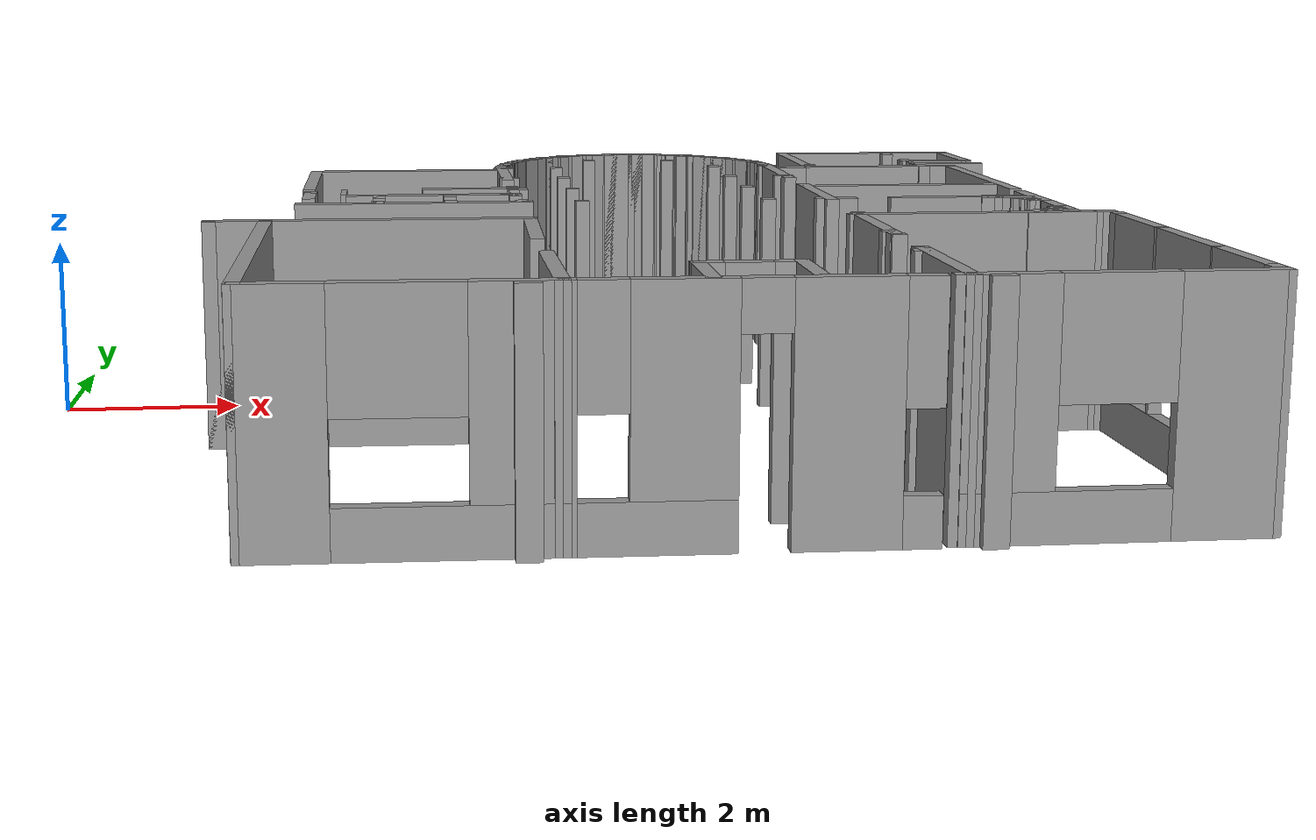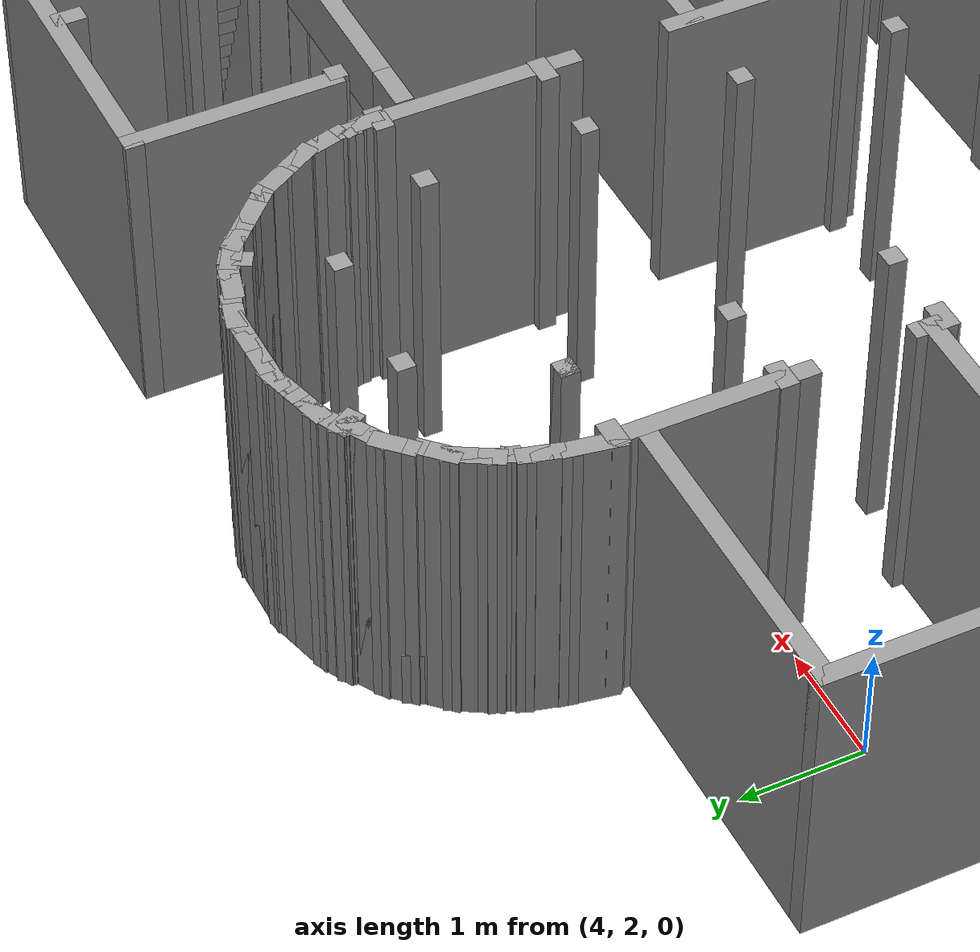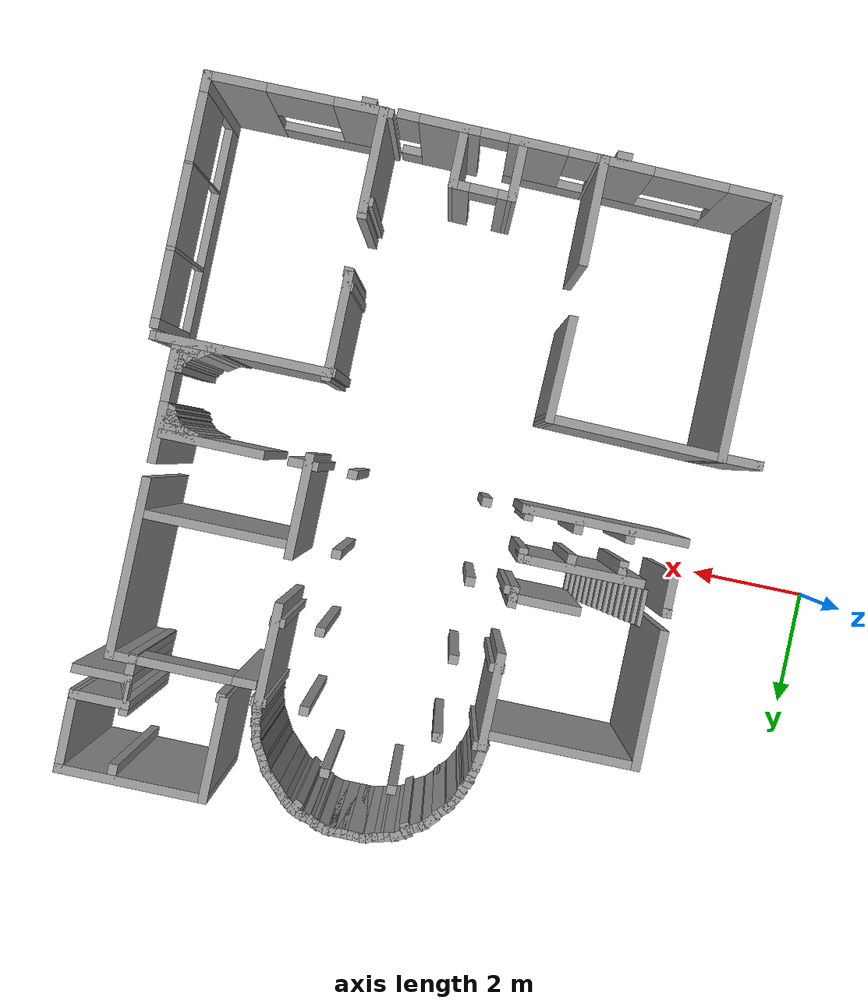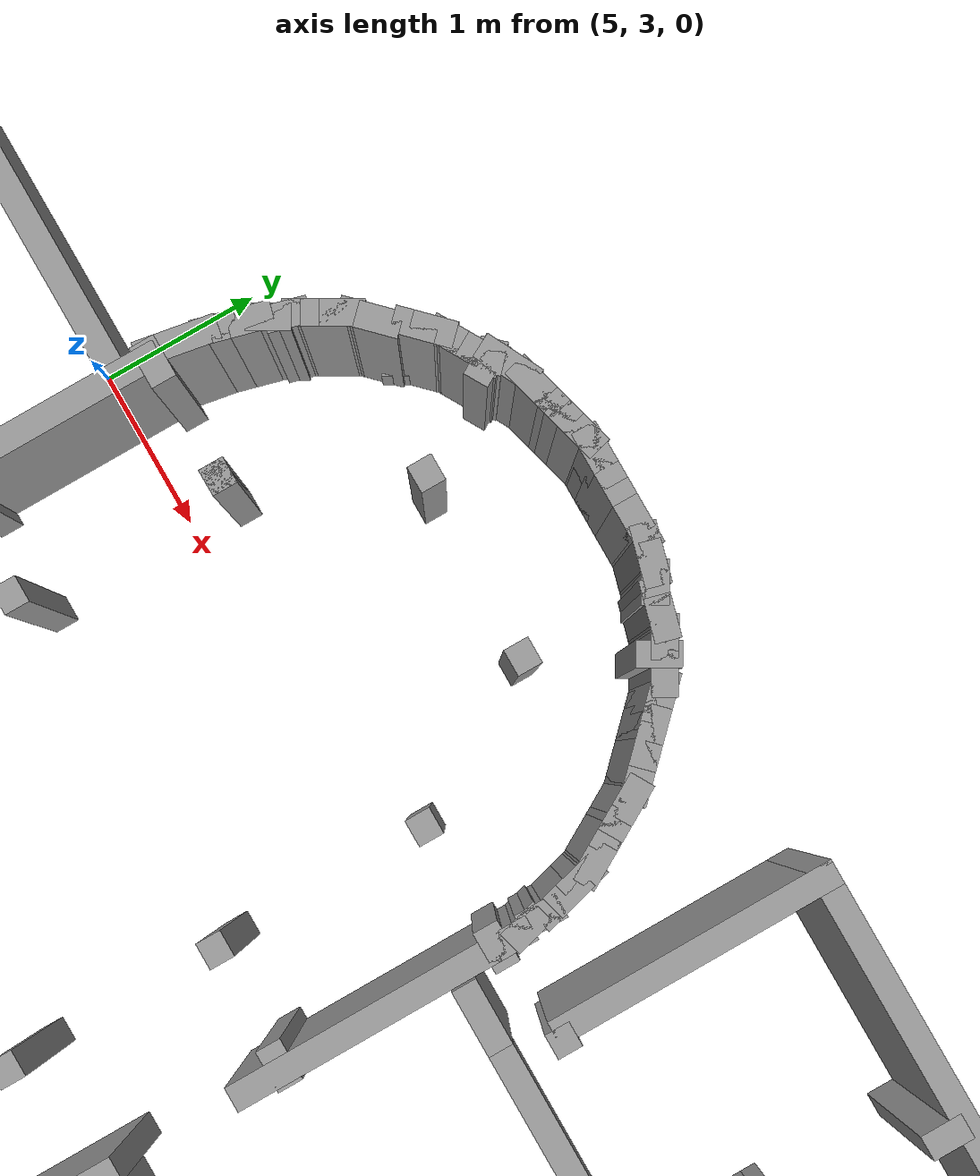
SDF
<?xml version='1.0'?>
<sdf version='1.6'>
  <model name='draft2'>
    <pose frame=''>6.97389 -0.64018 0 0 -0 0</pose>
    <link name='Stairs_0'>
      <visual name='Stairs_0_Visual_0'>
        <pose frame=''>-2.70588 1.24176 0.083333 0 -0 -1.5708</pose>
        <geometry>
          <box>
            <size>0.60325 0.069343 0.166667</size>
          </box>
        </geometry>
        <material>
          <script>
            <uri>file://media/materials/scripts/gazebo.material</uri>
            <name>Gazebo/Grey</name>
          </script>
          <ambient>1 1 1 1</ambient>
        </material>
      </visual>
      <collision name='Stairs_0_Collision_0'>
        <geometry>
          <box>
            <size>0.60325 0.069343 0.166667</size>
          </box>
        </geometry>
        <pose frame=''>-2.70588 1.24176 0.083333 0 -0 -1.5708</pose>
      </collision>
      <visual name='Stairs_0_Visual_1'>
        <pose frame=''>-2.77522 1.24176 0.25 0 -0 -1.5708</pose>
        <geometry>
          <box>
            <size>0.60325 0.069343 0.166667</size>
          </box>
        </geometry>
        <material>
          <script>
            <uri>file://media/materials/scripts/gazebo.material</uri>
            <name>Gazebo/Grey</name>
          </script>
          <ambient>1 1 1 1</ambient>
        </material>
      </visual>
      <collision name='Stairs_0_Collision_1'>
        <geometry>
          <box>
            <size>0.60325 0.069343 0.166667</size>
          </box>
        </geometry>
        <pose frame=''>-2.77522 1.24176 0.25 0 -0 -1.5708</pose>
      </collision>
      <visual name='Stairs_0_Visual_2'>
        <pose frame=''>-2.84456 1.24176 0.416667 0 -0 -1.5708</pose>
        <geometry>
          <box>
            <size>0.60325 0.069343 0.166667</size>
          </box>
        </geometry>
        <material>
          <script>
            <uri>file://media/materials/scripts/gazebo.material</uri>
            <name>Gazebo/Grey</name>
          </script>
          <ambient>1 1 1 1</ambient>
        </material>
      </visual>
      <collision name='Stairs_0_Collision_2'>
        <geometry>
          <box>
            <size>0.60325 0.069343 0.166667</size>
          </box>
        </geometry>
        <pose frame=''>-2.84456 1.24176 0.416667 0 -0 -1.5708</pose>
      </collision>
      <visual name='Stairs_0_Visual_3'>
        <pose frame=''>-2.91391 1.24176 0.583333 0 -0 -1.5708</pose>
        <geometry>
          <box>
            <size>0.60325 0.069343 0.166667</size>
          </box>
        </geometry>
        <material>
          <script>
            <uri>file://media/materials/scripts/gazebo.material</uri>
            <name>Gazebo/Grey</name>
          </script>
          <ambient>1 1 1 1</ambient>
        </material>
      </visual>
      <collision name='Stairs_0_Collision_3'>
        <geometry>
          <box>
            <size>0.60325 0.069343 0.166667</size>
          </box>
        </geometry>
        <pose frame=''>-2.91391 1.24176 0.583333 0 -0 -1.5708</pose>
      </collision>
      <visual name='Stairs_0_Visual_4'>
        <pose frame=''>-2.98325 1.24176 0.75 0 -0 -1.5708</pose>
        <geometry>
          <box>
            <size>0.60325 0.069343 0.166667</size>
          </box>
        </geometry>
        <material>
          <script>
            <uri>file://media/materials/scripts/gazebo.material</uri>
            <name>Gazebo/Grey</name>
          </script>
          <ambient>1 1 1 1</ambient>
        </material>
      </visual>
      <collision name='Stairs_0_Collision_4'>
        <geometry>
          <box>
            <size>0.60325 0.069343 0.166667</size>
          </box>
        </geometry>
        <pose frame=''>-2.98325 1.24176 0.75 0 -0 -1.5708</pose>
      </collision>
      <visual name='Stairs_0_Visual_5'>
        <pose frame=''>-3.05259 1.24176 0.916667 0 -0 -1.5708</pose>
        <geometry>
          <box>
            <size>0.60325 0.069343 0.166667</size>
          </box>
        </geometry>
        <material>
          <script>
            <uri>file://media/materials/scripts/gazebo.material</uri>
            <name>Gazebo/Grey</name>
          </script>
          <ambient>1 1 1 1</ambient>
        </material>
      </visual>
      <collision name='Stairs_0_Collision_5'>
        <geometry>
          <box>
            <size>0.60325 0.069343 0.166667</size>
          </box>
        </geometry>
        <pose frame=''>-3.05259 1.24176 0.916667 0 -0 -1.5708</pose>
      </collision>
      <visual name='Stairs_0_Visual_6'>
        <pose frame=''>-3.12194 1.24176 1.08333 0 -0 -1.5708</pose>
        <geometry>
          <box>
            <size>0.60325 0.069343 0.166667</size>
          </box>
        </geometry>
        <material>
          <script>
            <uri>file://media/materials/scripts/gazebo.material</uri>
            <name>Gazebo/Grey</name>
          </script>
          <ambient>1 1 1 1</ambient>
        </material>
      </visual>
      <collision name='Stairs_0_Collision_6'>
        <geometry>
          <box>
            <size>0.60325 0.069343 0.166667</size>
          </box>
        </geometry>
        <pose frame=''>-3.12194 1.24176 1.08333 0 -0 -1.5708</pose>
      </collision>
      <visual name='Stairs_0_Visual_7'>
        <pose frame=''>-3.19128 1.24176 1.25 0 -0 -1.5708</pose>
        <geometry>
          <box>
            <size>0.60325 0.069343 0.166667</size>
          </box>
        </geometry>
        <material>
          <script>
            <uri>file://media/materials/scripts/gazebo.material</uri>
            <name>Gazebo/Grey</name>
          </script>
          <ambient>1 1 1 1</ambient>
        </material>
      </visual>
      <collision name='Stairs_0_Collision_7'>
        <geometry>
          <box>
            <size>0.60325 0.069343 0.166667</size>
          </box>
        </geometry>
        <pose frame=''>-3.19128 1.24176 1.25 0 -0 -1.5708</pose>
      </collision>
      <visual name='Stairs_0_Visual_8'>
        <pose frame=''>-3.26062 1.24176 1.41667 0 -0 -1.5708</pose>
        <geometry>
          <box>
            <size>0.60325 0.069343 0.166667</size>
          </box>
        </geometry>
        <material>
          <script>
            <uri>file://media/materials/scripts/gazebo.material</uri>
            <name>Gazebo/Grey</name>
          </script>
          <ambient>1 1 1 1</ambient>
        </material>
      </visual>
      <collision name='Stairs_0_Collision_8'>
        <geometry>
          <box>
            <size>0.60325 0.069343 0.166667</size>
          </box>
        </geometry>
        <pose frame=''>-3.26062 1.24176 1.41667 0 -0 -1.5708</pose>
      </collision>
      <visual name='Stairs_0_Visual_9'>
        <pose frame=''>-3.32997 1.24176 1.58333 0 -0 -1.5708</pose>
        <geometry>
          <box>
            <size>0.60325 0.069343 0.166667</size>
          </box>
        </geometry>
        <material>
          <script>
            <uri>file://media/materials/scripts/gazebo.material</uri>
            <name>Gazebo/Grey</name>
          </script>
          <ambient>1 1 1 1</ambient>
        </material>
      </visual>
      <collision name='Stairs_0_Collision_9'>
        <geometry>
          <box>
            <size>0.60325 0.069343 0.166667</size>
          </box>
        </geometry>
        <pose frame=''>-3.32997 1.24176 1.58333 0 -0 -1.5708</pose>
      </collision>
      <visual name='Stairs_0_Visual_10'>
        <pose frame=''>-3.39931 1.24176 1.75 0 -0 -1.5708</pose>
        <geometry>
          <box>
            <size>0.60325 0.069343 0.166667</size>
          </box>
        </geometry>
        <material>
          <script>
            <uri>file://media/materials/scripts/gazebo.material</uri>
            <name>Gazebo/Grey</name>
          </script>
          <ambient>1 1 1 1</ambient>
        </material>
      </visual>
      <collision name='Stairs_0_Collision_10'>
        <geometry>
          <box>
            <size>0.60325 0.069343 0.166667</size>
          </box>
        </geometry>
        <pose frame=''>-3.39931 1.24176 1.75 0 -0 -1.5708</pose>
      </collision>
      <visual name='Stairs_0_Visual_11'>
        <pose frame=''>-3.46865 1.24176 1.91667 0 -0 -1.5708</pose>
        <geometry>
          <box>
            <size>0.60325 0.069343 0.166667</size>
          </box>
        </geometry>
        <material>
          <script>
            <uri>file://media/materials/scripts/gazebo.material</uri>
            <name>Gazebo/Grey</name>
          </script>
          <ambient>1 1 1 1</ambient>
        </material>
      </visual>
      <collision name='Stairs_0_Collision_11'>
        <geometry>
          <box>
            <size>0.60325 0.069343 0.166667</size>
          </box>
        </geometry>
        <pose frame=''>-3.46865 1.24176 1.91667 0 -0 -1.5708</pose>
      </collision>
      <visual name='Stairs_0_Visual_12'>
        <pose frame=''>-3.538 1.24176 2.08333 0 -0 -1.5708</pose>
        <geometry>
          <box>
            <size>0.60325 0.069343 0.166667</size>
          </box>
        </geometry>
        <material>
          <script>
            <uri>file://media/materials/scripts/gazebo.material</uri>
            <name>Gazebo/Grey</name>
          </script>
          <ambient>1 1 1 1</ambient>
        </material>
      </visual>
      <collision name='Stairs_0_Collision_12'>
        <geometry>
          <box>
            <size>0.60325 0.069343 0.166667</size>
          </box>
        </geometry>
        <pose frame=''>-3.538 1.24176 2.08333 0 -0 -1.5708</pose>
      </collision>
      <visual name='Stairs_0_Visual_13'>
        <pose frame=''>-3.60734 1.24176 2.25 0 -0 -1.5708</pose>
        <geometry>
          <box>
            <size>0.60325 0.069343 0.166667</size>
          </box>
        </geometry>
        <material>
          <script>
            <uri>file://media/materials/scripts/gazebo.material</uri>
            <name>Gazebo/Grey</name>
          </script>
          <ambient>1 1 1 1</ambient>
        </material>
      </visual>
      <collision name='Stairs_0_Collision_13'>
        <geometry>
          <box>
            <size>0.60325 0.069343 0.166667</size>
          </box>
        </geometry>
        <pose frame=''>-3.60734 1.24176 2.25 0 -0 -1.5708</pose>
      </collision>
      <visual name='Stairs_0_Visual_14'>
        <pose frame=''>-3.67668 1.24176 2.41667 0 -0 -1.5708</pose>
        <geometry>
          <box>
            <size>0.60325 0.069343 0.166667</size>
          </box>
        </geometry>
        <material>
          <script>
            <uri>file://media/materials/scripts/gazebo.material</uri>
            <name>Gazebo/Grey</name>
          </script>
          <ambient>1 1 1 1</ambient>
        </material>
      </visual>
      <collision name='Stairs_0_Collision_14'>
        <geometry>
          <box>
            <size>0.60325 0.069343 0.166667</size>
          </box>
        </geometry>
        <pose frame=''>-3.67668 1.24176 2.41667 0 -0 -1.5708</pose>
      </collision>
    </link>
    <link name='Stairs_1'>
      <visual name='Stairs_1_Visual_0'>
        <pose frame=''>5.01456 4.29354 0.083333 0 -0 -1.5708</pose>
        <geometry>
          <box>
            <size>0.352343 0.060625 0.166667</size>
          </box>
        </geometry>
        <material>
          <script>
            <uri>file://media/materials/scripts/gazebo.material</uri>
            <name>Gazebo/Grey</name>
          </script>
          <ambient>1 1 1 1</ambient>
        </material>
      </visual>
      <collision name='Stairs_1_Collision_0'>
        <geometry>
          <box>
            <size>0.352343 0.060625 0.166667</size>
          </box>
        </geometry>
        <pose frame=''>5.01456 4.29354 0.083333 0 -0 -1.5708</pose>
      </collision>
      <visual name='Stairs_1_Visual_1'>
        <pose frame=''>4.95394 4.29354 0.25 0 -0 -1.5708</pose>
        <geometry>
          <box>
            <size>0.352343 0.060625 0.166667</size>
          </box>
        </geometry>
        <material>
          <script>
            <uri>file://media/materials/scripts/gazebo.material</uri>
            <name>Gazebo/Grey</name>
          </script>
          <ambient>1 1 1 1</ambient>
        </material>
      </visual>
      <collision name='Stairs_1_Collision_1'>
        <geometry>
          <box>
            <size>0.352343 0.060625 0.166667</size>
          </box>
        </geometry>
        <pose frame=''>4.95394 4.29354 0.25 0 -0 -1.5708</pose>
      </collision>
      <visual name='Stairs_1_Visual_2'>
        <pose frame=''>4.89331 4.29354 0.416667 0 -0 -1.5708</pose>
        <geometry>
          <box>
            <size>0.352343 0.060625 0.166667</size>
          </box>
        </geometry>
        <material>
          <script>
            <uri>file://media/materials/scripts/gazebo.material</uri>
            <name>Gazebo/Grey</name>
          </script>
          <ambient>1 1 1 1</ambient>
        </material>
      </visual>
      <collision name='Stairs_1_Collision_2'>
        <geometry>
          <box>
            <size>0.352343 0.060625 0.166667</size>
          </box>
        </geometry>
        <pose frame=''>4.89331 4.29354 0.416667 0 -0 -1.5708</pose>
      </collision>
      <visual name='Stairs_1_Visual_3'>
        <pose frame=''>4.83269 4.29354 0.583333 0 -0 -1.5708</pose>
        <geometry>
          <box>
            <size>0.352343 0.060625 0.166667</size>
          </box>
        </geometry>
        <material>
          <script>
            <uri>file://media/materials/scripts/gazebo.material</uri>
            <name>Gazebo/Grey</name>
          </script>
          <ambient>1 1 1 1</ambient>
        </material>
      </visual>
      <collision name='Stairs_1_Collision_3'>
        <geometry>
          <box>
            <size>0.352343 0.060625 0.166667</size>
          </box>
        </geometry>
        <pose frame=''>4.83269 4.29354 0.583333 0 -0 -1.5708</pose>
      </collision>
      <visual name='Stairs_1_Visual_4'>
        <pose frame=''>4.77206 4.29354 0.75 0 -0 -1.5708</pose>
        <geometry>
          <box>
            <size>0.352343 0.060625 0.166667</size>
          </box>
        </geometry>
        <material>
          <script>
            <uri>file://media/materials/scripts/gazebo.material</uri>
            <name>Gazebo/Grey</name>
          </script>
          <ambient>1 1 1 1</ambient>
        </material>
      </visual>
      <collision name='Stairs_1_Collision_4'>
        <geometry>
          <box>
            <size>0.352343 0.060625 0.166667</size>
          </box>
        </geometry>
        <pose frame=''>4.77206 4.29354 0.75 0 -0 -1.5708</pose>
      </collision>
      <visual name='Stairs_1_Visual_5'>
        <pose frame=''>4.71144 4.29354 0.916667 0 -0 -1.5708</pose>
        <geometry>
          <box>
            <size>0.352343 0.060625 0.166667</size>
          </box>
        </geometry>
        <material>
          <script>
            <uri>file://media/materials/scripts/gazebo.material</uri>
            <name>Gazebo/Grey</name>
          </script>
          <ambient>1 1 1 1</ambient>
        </material>
      </visual>
      <collision name='Stairs_1_Collision_5'>
        <geometry>
          <box>
            <size>0.352343 0.060625 0.166667</size>
          </box>
        </geometry>
        <pose frame=''>4.71144 4.29354 0.916667 0 -0 -1.5708</pose>
      </collision>
      <visual name='Stairs_1_Visual_6'>
        <pose frame=''>4.65081 4.29354 1.08333 0 -0 -1.5708</pose>
        <geometry>
          <box>
            <size>0.352343 0.060625 0.166667</size>
          </box>
        </geometry>
        <material>
          <script>
            <uri>file://media/materials/scripts/gazebo.material</uri>
            <name>Gazebo/Grey</name>
          </script>
          <ambient>1 1 1 1</ambient>
        </material>
      </visual>
      <collision name='Stairs_1_Collision_6'>
        <geometry>
          <box>
            <size>0.352343 0.060625 0.166667</size>
          </box>
        </geometry>
        <pose frame=''>4.65081 4.29354 1.08333 0 -0 -1.5708</pose>
      </collision>
      <visual name='Stairs_1_Visual_7'>
        <pose frame=''>4.59019 4.29354 1.25 0 -0 -1.5708</pose>
        <geometry>
          <box>
            <size>0.352343 0.060625 0.166667</size>
          </box>
        </geometry>
        <material>
          <script>
            <uri>file://media/materials/scripts/gazebo.material</uri>
            <name>Gazebo/Grey</name>
          </script>
          <ambient>1 1 1 1</ambient>
        </material>
      </visual>
      <collision name='Stairs_1_Collision_7'>
        <geometry>
          <box>
            <size>0.352343 0.060625 0.166667</size>
          </box>
        </geometry>
        <pose frame=''>4.59019 4.29354 1.25 0 -0 -1.5708</pose>
      </collision>
      <visual name='Stairs_1_Visual_8'>
        <pose frame=''>4.52956 4.29354 1.41667 0 -0 -1.5708</pose>
        <geometry>
          <box>
            <size>0.352343 0.060625 0.166667</size>
          </box>
        </geometry>
        <material>
          <script>
            <uri>file://media/materials/scripts/gazebo.material</uri>
            <name>Gazebo/Grey</name>
          </script>
          <ambient>1 1 1 1</ambient>
        </material>
      </visual>
      <collision name='Stairs_1_Collision_8'>
        <geometry>
          <box>
            <size>0.352343 0.060625 0.166667</size>
          </box>
        </geometry>
        <pose frame=''>4.52956 4.29354 1.41667 0 -0 -1.5708</pose>
      </collision>
      <visual name='Stairs_1_Visual_9'>
        <pose frame=''>4.46894 4.29354 1.58333 0 -0 -1.5708</pose>
        <geometry>
          <box>
            <size>0.352343 0.060625 0.166667</size>
          </box>
        </geometry>
        <material>
          <script>
            <uri>file://media/materials/scripts/gazebo.material</uri>
            <name>Gazebo/Grey</name>
          </script>
          <ambient>1 1 1 1</ambient>
        </material>
      </visual>
      <collision name='Stairs_1_Collision_9'>
        <geometry>
          <box>
            <size>0.352343 0.060625 0.166667</size>
          </box>
        </geometry>
        <pose frame=''>4.46894 4.29354 1.58333 0 -0 -1.5708</pose>
      </collision>
      <visual name='Stairs_1_Visual_10'>
        <pose frame=''>4.40831 4.29354 1.75 0 -0 -1.5708</pose>
        <geometry>
          <box>
            <size>0.352343 0.060625 0.166667</size>
          </box>
        </geometry>
        <material>
          <script>
            <uri>file://media/materials/scripts/gazebo.material</uri>
            <name>Gazebo/Grey</name>
          </script>
          <ambient>1 1 1 1</ambient>
        </material>
      </visual>
      <collision name='Stairs_1_Collision_10'>
        <geometry>
          <box>
            <size>0.352343 0.060625 0.166667</size>
          </box>
        </geometry>
        <pose frame=''>4.40831 4.29354 1.75 0 -0 -1.5708</pose>
      </collision>
      <visual name='Stairs_1_Visual_11'>
        <pose frame=''>4.34769 4.29354 1.91667 0 -0 -1.5708</pose>
        <geometry>
          <box>
            <size>0.352343 0.060625 0.166667</size>
          </box>
        </geometry>
        <material>
          <script>
            <uri>file://media/materials/scripts/gazebo.material</uri>
            <name>Gazebo/Grey</name>
          </script>
          <ambient>1 1 1 1</ambient>
        </material>
      </visual>
      <collision name='Stairs_1_Collision_11'>
        <geometry>
          <box>
            <size>0.352343 0.060625 0.166667</size>
          </box>
        </geometry>
        <pose frame=''>4.34769 4.29354 1.91667 0 -0 -1.5708</pose>
      </collision>
      <visual name='Stairs_1_Visual_12'>
        <pose frame=''>4.28706 4.29354 2.08333 0 -0 -1.5708</pose>
        <geometry>
          <box>
            <size>0.352343 0.060625 0.166667</size>
          </box>
        </geometry>
        <material>
          <script>
            <uri>file://media/materials/scripts/gazebo.material</uri>
            <name>Gazebo/Grey</name>
          </script>
          <ambient>1 1 1 1</ambient>
        </material>
      </visual>
      <collision name='Stairs_1_Collision_12'>
        <geometry>
          <box>
            <size>0.352343 0.060625 0.166667</size>
          </box>
        </geometry>
        <pose frame=''>4.28706 4.29354 2.08333 0 -0 -1.5708</pose>
      </collision>
      <visual name='Stairs_1_Visual_13'>
        <pose frame=''>4.22644 4.29354 2.25 0 -0 -1.5708</pose>
        <geometry>
          <box>
            <size>0.352343 0.060625 0.166667</size>
          </box>
        </geometry>
        <material>
          <script>
            <uri>file://media/materials/scripts/gazebo.material</uri>
            <name>Gazebo/Grey</name>
          </script>
          <ambient>1 1 1 1</ambient>
        </material>
      </visual>
      <collision name='Stairs_1_Collision_13'>
        <geometry>
          <box>
            <size>0.352343 0.060625 0.166667</size>
          </box>
        </geometry>
        <pose frame=''>4.22644 4.29354 2.25 0 -0 -1.5708</pose>
      </collision>
      <visual name='Stairs_1_Visual_14'>
        <pose frame=''>4.16582 4.29354 2.41667 0 -0 -1.5708</pose>
        <geometry>
          <box>
            <size>0.352343 0.060625 0.166667</size>
          </box>
        </geometry>
        <material>
          <script>
            <uri>file://media/materials/scripts/gazebo.material</uri>
            <name>Gazebo/Grey</name>
          </script>
          <ambient>1 1 1 1</ambient>
        </material>
      </visual>
      <collision name='Stairs_1_Collision_14'>
        <geometry>
          <box>
            <size>0.352343 0.060625 0.166667</size>
          </box>
        </geometry>
        <pose frame=''>4.16582 4.29354 2.41667 0 -0 -1.5708</pose>
      </collision>
    </link>
    <link name='Wall_0'>
      <collision name='Wall_0_Collision'>
        <geometry>
          <box>
            <size>4.40748 0.15 2.5</size>
          </box>
        </geometry>
        <pose frame=''>0 0 1.25 0 -0 0</pose>
      </collision>
      <visual name='Wall_0_Visual'>
        <pose frame=''>0 0 1.25 0 -0 0</pose>
        <geometry>
          <box>
            <size>4.40748 0.15 2.5</size>
          </box>
        </geometry>
        <material>
          <script>
            <uri>file://media/materials/scripts/gazebo.material</uri>
            <name>Gazebo/Grey</name>
          </script>
          <ambient>1 1 1 1</ambient>
        </material>
      </visual>
      <pose frame=''>-4.43924 -3.52153 0 0 0 -1.5708</pose>
    </link>
    <link name='Wall_1'>
      <collision name='Wall_1_Collision'>
        <geometry>
          <box>
            <size>0.15 0.15 2.5</size>
          </box>
        </geometry>
        <pose frame=''>0 0 1.25 0 -0 0</pose>
      </collision>
      <visual name='Wall_1_Visual'>
        <pose frame=''>0 0 1.25 0 -0 0</pose>
        <geometry>
          <box>
            <size>0.15 0.15 2.5</size>
          </box>
        </geometry>
        <material>
          <script>
            <uri>file://media/materials/scripts/gazebo.material</uri>
            <name>Gazebo/Grey</name>
          </script>
          <ambient>1 1 1 1</ambient>
        </material>
      </visual>
      <pose frame=''>-4.43924 -5.65027 0 0 -0 0</pose>
    </link>
    <link name='Wall_10'>
      <collision name='Wall_10_Collision'>
        <geometry>
          <box>
            <size>0.16 0.15 2.5</size>
          </box>
        </geometry>
        <pose frame=''>0 0 1.25 0 -0 0</pose>
      </collision>
      <visual name='Wall_10_Visual'>
        <pose frame=''>0 0 1.25 0 -0 0</pose>
        <geometry>
          <box>
            <size>0.16 0.15 2.5</size>
          </box>
        </geometry>
        <material>
          <script>
            <uri>file://media/materials/scripts/gazebo.material</uri>
            <name>Gazebo/Grey</name>
          </script>
          <ambient>1 1 1 1</ambient>
        </material>
      </visual>
      <pose frame=''>-4.08069 1.24095 0 0 -0 0</pose>
    </link>
    <link name='Wall_107'>
      <collision name='Wall_107_Collision'>
        <geometry>
          <box>
            <size>0.25 0.15 2.5</size>
          </box>
        </geometry>
        <pose frame=''>0 0 1.25 0 -0 0</pose>
      </collision>
      <visual name='Wall_107_Visual'>
        <pose frame=''>0 0 1.25 0 -0 0</pose>
        <geometry>
          <box>
            <size>0.25 0.15 2.5</size>
          </box>
        </geometry>
        <material>
          <script>
            <uri>file://media/materials/scripts/gazebo.material</uri>
            <name>Gazebo/Grey</name>
          </script>
          <ambient>1 1 1 1</ambient>
        </material>
      </visual>
      <pose frame=''>-1.58806 3.9678 0 0 -0 3.14159</pose>
    </link>
    <link name='Wall_109'>
      <collision name='Wall_109_Collision'>
        <geometry>
          <box>
            <size>0.25 0.15 2.5</size>
          </box>
        </geometry>
        <pose frame=''>0 0 1.25 0 -0 0</pose>
      </collision>
      <visual name='Wall_109_Visual'>
        <pose frame=''>0 0 1.25 0 -0 0</pose>
        <geometry>
          <box>
            <size>0.25 0.15 2.5</size>
          </box>
        </geometry>
        <material>
          <script>
            <uri>file://media/materials/scripts/gazebo.material</uri>
            <name>Gazebo/Grey</name>
          </script>
          <ambient>1 1 1 1</ambient>
        </material>
      </visual>
      <pose frame=''>-1.58806 2.67781 0 0 -0 0</pose>
    </link>
    <link name='Wall_11'>
      <collision name='Wall_11_Collision'>
        <geometry>
          <box>
            <size>0.75 0.15 2.5</size>
          </box>
        </geometry>
        <pose frame=''>0 0 1.25 0 -0 0</pose>
      </collision>
      <visual name='Wall_11_Visual'>
        <pose frame=''>0 0 1.25 0 -0 0</pose>
        <geometry>
          <box>
            <size>0.75 0.15 2.5</size>
          </box>
        </geometry>
        <material>
          <script>
            <uri>file://media/materials/scripts/gazebo.material</uri>
            <name>Gazebo/Grey</name>
          </script>
          <ambient>1 1 1 1</ambient>
        </material>
      </visual>
      <pose frame=''>-4.07569 0.940948 0 0 0 -1.5708</pose>
    </link>
    <link name='Wall_112'>
      <collision name='Wall_112_Collision'>
        <geometry>
          <box>
            <size>0.25 0.15 2.5</size>
          </box>
        </geometry>
        <pose frame=''>0 0 1.25 0 -0 0</pose>
      </collision>
      <visual name='Wall_112_Visual'>
        <pose frame=''>0 0 1.25 0 -0 0</pose>
        <geometry>
          <box>
            <size>0.25 0.15 2.5</size>
          </box>
        </geometry>
        <material>
          <script>
            <uri>file://media/materials/scripts/gazebo.material</uri>
            <name>Gazebo/Grey</name>
          </script>
          <ambient>1 1 1 1</ambient>
        </material>
      </visual>
      <pose frame=''>1.12694 5.5445 0 0 0 -2.0944</pose>
    </link>
    <link name='Wall_114'>
      <collision name='Wall_114_Collision'>
        <geometry>
          <box>
            <size>0.25 0.15 2.5</size>
          </box>
        </geometry>
        <pose frame=''>0 0 1.25 0 -0 0</pose>
      </collision>
      <visual name='Wall_114_Visual'>
        <pose frame=''>0 0 1.25 0 -0 0</pose>
        <geometry>
          <box>
            <size>0.25 0.15 2.5</size>
          </box>
        </geometry>
        <material>
          <script>
            <uri>file://media/materials/scripts/gazebo.material</uri>
            <name>Gazebo/Grey</name>
          </script>
          <ambient>1 1 1 1</ambient>
        </material>
      </visual>
      <pose frame=''>2.05194 4.00781 0 0 -0 3.14159</pose>
    </link>
    <link name='Wall_116'>
      <collision name='Wall_116_Collision'>
        <geometry>
          <box>
            <size>0.25 0.15 2.5</size>
          </box>
        </geometry>
        <pose frame=''>0 0 1.25 0 -0 0</pose>
      </collision>
      <visual name='Wall_116_Visual'>
        <pose frame=''>0 0 1.25 0 -0 0</pose>
        <geometry>
          <box>
            <size>0.25 0.15 2.5</size>
          </box>
        </geometry>
        <material>
          <script>
            <uri>file://media/materials/scripts/gazebo.material</uri>
            <name>Gazebo/Grey</name>
          </script>
          <ambient>1 1 1 1</ambient>
        </material>
      </visual>
      <pose frame=''>2.02194 2.6878 0 0 -0 3.14159</pose>
    </link>
    <link name='Wall_123'>
      <collision name='Wall_123_Collision'>
        <geometry>
          <box>
            <size>0.16 0.15 2.5</size>
          </box>
        </geometry>
        <pose frame=''>0 0 1.25 0 -0 0</pose>
      </collision>
      <visual name='Wall_123_Visual'>
        <pose frame=''>0 0 1.25 0 -0 0</pose>
        <geometry>
          <box>
            <size>0.16 0.15 2.5</size>
          </box>
        </geometry>
        <material>
          <script>
            <uri>file://media/materials/scripts/gazebo.material</uri>
            <name>Gazebo/Grey</name>
          </script>
          <ambient>1 1 1 1</ambient>
        </material>
      </visual>
      <pose frame=''>-0.877885 3.96618 0 0 -0 0</pose>
    </link>
    <link name='Wall_124'>
      <collision name='Wall_124_Collision'>
        <geometry>
          <box>
            <size>0.16 0.15 2.5</size>
          </box>
        </geometry>
        <pose frame=''>0 0 1.25 0 -0 0</pose>
      </collision>
      <visual name='Wall_124_Visual'>
        <pose frame=''>0 0 1.25 0 -0 0</pose>
        <geometry>
          <box>
            <size>0.16 0.15 2.5</size>
          </box>
        </geometry>
        <material>
          <script>
            <uri>file://media/materials/scripts/gazebo.material</uri>
            <name>Gazebo/Grey</name>
          </script>
          <ambient>1 1 1 1</ambient>
        </material>
      </visual>
      <pose frame=''>-0.877885 3.96618 0 0 -0 3.14159</pose>
    </link>
    <link name='Wall_127'>
      <collision name='Wall_127_Collision'>
        <geometry>
          <box>
            <size>0.16 0.15 2.5</size>
          </box>
        </geometry>
        <pose frame=''>0 0 1.25 0 -0 0</pose>
      </collision>
      <visual name='Wall_127_Visual'>
        <pose frame=''>0 0 1.25 0 -0 0</pose>
        <geometry>
          <box>
            <size>0.16 0.15 2.5</size>
          </box>
        </geometry>
        <material>
          <script>
            <uri>file://media/materials/scripts/gazebo.material</uri>
            <name>Gazebo/Grey</name>
          </script>
          <ambient>1 1 1 1</ambient>
        </material>
      </visual>
      <pose frame=''>-0.335407 4.94454 0 0 -0 0</pose>
    </link>
    <link name='Wall_129'>
      <collision name='Wall_129_Collision'>
        <geometry>
          <box>
            <size>0.16 0.15 2.5</size>
          </box>
        </geometry>
        <pose frame=''>0 0 1.25 0 -0 0</pose>
      </collision>
      <visual name='Wall_129_Visual'>
        <pose frame=''>0 0 1.25 0 -0 0</pose>
        <geometry>
          <box>
            <size>0.16 0.15 2.5</size>
          </box>
        </geometry>
        <material>
          <script>
            <uri>file://media/materials/scripts/gazebo.material</uri>
            <name>Gazebo/Grey</name>
          </script>
          <ambient>1 1 1 1</ambient>
        </material>
      </visual>
      <pose frame=''>-0.877632 2.68306 0 0 -0 0</pose>
    </link>
    <link name='Wall_13'>
      <collision name='Wall_13_Collision'>
        <geometry>
          <box>
            <size>2 0.15 2.5</size>
          </box>
        </geometry>
        <pose frame=''>0 0 1.25 0 -0 0</pose>
      </collision>
      <visual name='Wall_13_Visual'>
        <pose frame=''>0 0 1.25 0 -0 0</pose>
        <geometry>
          <box>
            <size>2 0.15 2.5</size>
          </box>
        </geometry>
        <material>
          <script>
            <uri>file://media/materials/scripts/gazebo.material</uri>
            <name>Gazebo/Grey</name>
          </script>
          <ambient>1 1 1 1</ambient>
        </material>
      </visual>
      <pose frame=''>-2.64319 0.861448 0 0 -0 0</pose>
    </link>
    <link name='Wall_131'>
      <collision name='Wall_131_Collision'>
        <geometry>
          <box>
            <size>0.16 0.15 2.5</size>
          </box>
        </geometry>
        <pose frame=''>0 0 1.25 0 -0 0</pose>
      </collision>
      <visual name='Wall_131_Visual'>
        <pose frame=''>0 0 1.25 0 -0 0</pose>
        <geometry>
          <box>
            <size>0.16 0.15 2.5</size>
          </box>
        </geometry>
        <material>
          <script>
            <uri>file://media/materials/scripts/gazebo.material</uri>
            <name>Gazebo/Grey</name>
          </script>
          <ambient>1 1 1 1</ambient>
        </material>
      </visual>
      <pose frame=''>-0.877632 1.40024 0 0 -0 0</pose>
    </link>
    <link name='Wall_133'>
      <collision name='Wall_133_Collision'>
        <geometry>
          <box>
            <size>0.16 0.15 2.5</size>
          </box>
        </geometry>
        <pose frame=''>0 0 1.25 0 -0 0</pose>
      </collision>
      <visual name='Wall_133_Visual'>
        <pose frame=''>0 0 1.25 0 -0 0</pose>
        <geometry>
          <box>
            <size>0.16 0.15 2.5</size>
          </box>
        </geometry>
        <material>
          <script>
            <uri>file://media/materials/scripts/gazebo.material</uri>
            <name>Gazebo/Grey</name>
          </script>
          <ambient>1 1 1 1</ambient>
        </material>
      </visual>
      <pose frame=''>-0.877632 0.090964 0 0 -0 0</pose>
    </link>
    <link name='Wall_135'>
      <collision name='Wall_135_Collision'>
        <geometry>
          <box>
            <size>0.16 0.15 2.5</size>
          </box>
        </geometry>
        <pose frame=''>0 0 1.25 0 -0 0</pose>
      </collision>
      <visual name='Wall_135_Visual'>
        <pose frame=''>0 0 1.25 0 -0 0</pose>
        <geometry>
          <box>
            <size>0.16 0.15 2.5</size>
          </box>
        </geometry>
        <material>
          <script>
            <uri>file://media/materials/scripts/gazebo.material</uri>
            <name>Gazebo/Grey</name>
          </script>
          <ambient>1 1 1 1</ambient>
        </material>
      </visual>
      <pose frame=''>0.775493 4.90486 0 0 -0 0</pose>
    </link>
    <link name='Wall_137'>
      <collision name='Wall_137_Collision'>
        <geometry>
          <box>
            <size>0.16 0.15 2.5</size>
          </box>
        </geometry>
        <pose frame=''>0 0 1.25 0 -0 0</pose>
      </collision>
      <visual name='Wall_137_Visual'>
        <pose frame=''>0 0 1.25 0 -0 0</pose>
        <geometry>
          <box>
            <size>0.16 0.15 2.5</size>
          </box>
        </geometry>
        <material>
          <script>
            <uri>file://media/materials/scripts/gazebo.material</uri>
            <name>Gazebo/Grey</name>
          </script>
          <ambient>1 1 1 1</ambient>
        </material>
      </visual>
      <pose frame=''>1.30449 3.99234 0 0 -0 0</pose>
    </link>
    <link name='Wall_139'>
      <collision name='Wall_139_Collision'>
        <geometry>
          <box>
            <size>0.16 0.15 2.5</size>
          </box>
        </geometry>
        <pose frame=''>0 0 1.25 0 -0 0</pose>
      </collision>
      <visual name='Wall_139_Visual'>
        <pose frame=''>0 0 1.25 0 -0 0</pose>
        <geometry>
          <box>
            <size>0.16 0.15 2.5</size>
          </box>
        </geometry>
        <material>
          <script>
            <uri>file://media/materials/scripts/gazebo.material</uri>
            <name>Gazebo/Grey</name>
          </script>
          <ambient>1 1 1 1</ambient>
        </material>
      </visual>
      <pose frame=''>1.31772 2.69629 0 0 -0 0</pose>
    </link>
    <link name='Wall_141'>
      <collision name='Wall_141_Collision'>
        <geometry>
          <box>
            <size>0.16 0.15 2.5</size>
          </box>
        </geometry>
        <pose frame=''>0 0 1.25 0 -0 0</pose>
      </collision>
      <visual name='Wall_141_Visual'>
        <pose frame=''>0 0 1.25 0 -0 0</pose>
        <geometry>
          <box>
            <size>0.16 0.15 2.5</size>
          </box>
        </geometry>
        <material>
          <script>
            <uri>file://media/materials/scripts/gazebo.material</uri>
            <name>Gazebo/Grey</name>
          </script>
          <ambient>1 1 1 1</ambient>
        </material>
      </visual>
      <pose frame=''>1.31772 1.41346 0 0 -0 0</pose>
    </link>
    <link name='Wall_143'>
      <collision name='Wall_143_Collision'>
        <geometry>
          <box>
            <size>0.16 0.15 2.5</size>
          </box>
        </geometry>
        <pose frame=''>0 0 1.25 0 -0 0</pose>
      </collision>
      <visual name='Wall_143_Visual'>
        <pose frame=''>0 0 1.25 0 -0 0</pose>
        <geometry>
          <box>
            <size>0.16 0.15 2.5</size>
          </box>
        </geometry>
        <material>
          <script>
            <uri>file://media/materials/scripts/gazebo.material</uri>
            <name>Gazebo/Grey</name>
          </script>
          <ambient>1 1 1 1</ambient>
        </material>
      </visual>
      <pose frame=''>1.33094 0.104189 0 0 -0 0</pose>
    </link>
    <link name='Wall_145'>
      <collision name='Wall_145_Collision'>
        <geometry>
          <box>
            <size>1.75 0.15 2.5</size>
          </box>
        </geometry>
        <pose frame=''>0 0 1.25 0 -0 0</pose>
      </collision>
      <visual name='Wall_145_Visual'>
        <pose frame=''>0 0 1.25 0 -0 0</pose>
        <geometry>
          <box>
            <size>1.75 0.15 2.5</size>
          </box>
        </geometry>
        <material>
          <script>
            <uri>file://media/materials/scripts/gazebo.material</uri>
            <name>Gazebo/Grey</name>
          </script>
          <ambient>1 1 1 1</ambient>
        </material>
      </visual>
      <pose frame=''>2.06654 0.785389 0 0 0 -1.5708</pose>
    </link>
    <link name='Wall_152'>
      <collision name='Wall_152_Collision'>
        <geometry>
          <box>
            <size>0.5 0.15 2.5</size>
          </box>
        </geometry>
        <pose frame=''>0 0 1.25 0 -0 0</pose>
      </collision>
      <visual name='Wall_152_Visual'>
        <pose frame=''>0 0 1.25 0 -0 0</pose>
        <geometry>
          <box>
            <size>0.5 0.15 2.5</size>
          </box>
        </geometry>
        <material>
          <script>
            <uri>file://media/materials/scripts/gazebo.material</uri>
            <name>Gazebo/Grey</name>
          </script>
          <ambient>1 1 1 1</ambient>
        </material>
      </visual>
      <pose frame=''>2.14574 0.104189 0 0 -0 0</pose>
    </link>
    <link name='Wall_157'>
      <pose frame=''>3.39107 3.75429 0 0 -0 3.14159</pose>
      <visual name='Wall_157_Visual_0'>
        <pose frame=''>-0.982829 0 1.25 0 -0 0</pose>
        <geometry>
          <box>
            <size>0.534342 0.15 2.5</size>
          </box>
        </geometry>
        <material>
          <script>
            <uri>file://media/materials/scripts/gazebo.material</uri>
            <name>Gazebo/Grey</name>
          </script>
          <ambient>1 1 1 1</ambient>
        </material>
      </visual>
      <collision name='Wall_157_Collision_0'>
        <geometry>
          <box>
            <size>0.534342 0.15 2.5</size>
          </box>
        </geometry>
        <pose frame=''>-0.982829 0 1.25 0 -0 0</pose>
      </collision>
      <visual name='Wall_157_Visual_1'>
        <pose frame=''>1.04948 0 1.25 0 -0 0</pose>
        <geometry>
          <box>
            <size>0.401036 0.15 2.5</size>
          </box>
        </geometry>
        <material>
          <script>
            <uri>file://media/materials/scripts/gazebo.material</uri>
            <name>Gazebo/Grey</name>
          </script>
          <ambient>1 1 1 1</ambient>
        </material>
      </visual>
      <collision name='Wall_157_Collision_1'>
        <geometry>
          <box>
            <size>0.401036 0.15 2.5</size>
          </box>
        </geometry>
        <pose frame=''>1.04948 0 1.25 0 -0 0</pose>
      </collision>
      <visual name='Wall_157_Visual_2'>
        <pose frame=''>0.066653 0 2.25 0 -0 0</pose>
        <geometry>
          <box>
            <size>1.56462 0.15 0.5</size>
          </box>
        </geometry>
        <material>
          <script>
            <uri>file://media/materials/scripts/gazebo.material</uri>
            <name>Gazebo/Grey</name>
          </script>
          <ambient>1 1 1 1</ambient>
        </material>
      </visual>
      <collision name='Wall_157_Collision_2'>
        <geometry>
          <box>
            <size>1.56462 0.15 0.5</size>
          </box>
        </geometry>
        <pose frame=''>0.066653 0 2.25 0 -0 0</pose>
      </collision>
    </link>
    <link name='Wall_159'>
      <collision name='Wall_159_Collision'>
        <geometry>
          <box>
            <size>3 0.15 2.5</size>
          </box>
        </geometry>
        <pose frame=''>0 0 1.25 0 -0 0</pose>
      </collision>
      <visual name='Wall_159_Visual'>
        <pose frame=''>0 0 1.25 0 -0 0</pose>
        <geometry>
          <box>
            <size>3 0.15 2.5</size>
          </box>
        </geometry>
        <material>
          <script>
            <uri>file://media/materials/scripts/gazebo.material</uri>
            <name>Gazebo/Grey</name>
          </script>
          <ambient>1 1 1 1</ambient>
        </material>
      </visual>
      <pose frame=''>4.56607 2.32929 0 0 0 -1.5708</pose>
    </link>
    <link name='Wall_16'>
      <collision name='Wall_16_Collision'>
        <geometry>
          <box>
            <size>0.25 0.15 2.5</size>
          </box>
        </geometry>
        <pose frame=''>0 0 1.25 0 -0 0</pose>
      </collision>
      <visual name='Wall_16_Visual'>
        <pose frame=''>0 0 1.25 0 -0 0</pose>
        <geometry>
          <box>
            <size>0.25 0.15 2.5</size>
          </box>
        </geometry>
        <material>
          <script>
            <uri>file://media/materials/scripts/gazebo.material</uri>
            <name>Gazebo/Grey</name>
          </script>
          <ambient>1 1 1 1</ambient>
        </material>
      </visual>
      <pose frame=''>-1.66819 0.861448 0 0 -0 0</pose>
    </link>
    <link name='Wall_161'>
      <pose frame=''>4.53962 -0.402141 0 0 0 -1.5708</pose>
      <visual name='Wall_161_Visual_0'>
        <pose frame=''>-0.491085 0 1.25 0 -0 0</pose>
        <geometry>
          <box>
            <size>1.01783 0.15 2.5</size>
          </box>
        </geometry>
        <material>
          <script>
            <uri>file://media/materials/scripts/gazebo.material</uri>
            <name>Gazebo/Grey</name>
          </script>
          <ambient>1 1 1 1</ambient>
        </material>
      </visual>
      <collision name='Wall_161_Collision_0'>
        <geometry>
          <box>
            <size>1.01783 0.15 2.5</size>
          </box>
        </geometry>
        <pose frame=''>-0.491085 0 1.25 0 -0 0</pose>
      </collision>
      <visual name='Wall_161_Visual_1'>
        <pose frame=''>0.758915 0 1.25 0 -0 0</pose>
        <geometry>
          <box>
            <size>0.482171 0.15 2.5</size>
          </box>
        </geometry>
        <material>
          <script>
            <uri>file://media/materials/scripts/gazebo.material</uri>
            <name>Gazebo/Grey</name>
          </script>
          <ambient>1 1 1 1</ambient>
        </material>
      </visual>
      <collision name='Wall_161_Collision_1'>
        <geometry>
          <box>
            <size>0.482171 0.15 2.5</size>
          </box>
        </geometry>
        <pose frame=''>0.758915 0 1.25 0 -0 0</pose>
      </collision>
      <visual name='Wall_161_Visual_2'>
        <pose frame=''>0.267829 0 2.25 0 -0 0</pose>
        <geometry>
          <box>
            <size>0.5 0.15 0.5</size>
          </box>
        </geometry>
        <material>
          <script>
            <uri>file://media/materials/scripts/gazebo.material</uri>
            <name>Gazebo/Grey</name>
          </script>
          <ambient>1 1 1 1</ambient>
        </material>
      </visual>
      <collision name='Wall_161_Collision_2'>
        <geometry>
          <box>
            <size>0.5 0.15 0.5</size>
          </box>
        </geometry>
        <pose frame=''>0.267829 0 2.25 0 -0 0</pose>
      </collision>
    </link>
    <link name='Wall_169'>
      <collision name='Wall_169_Collision'>
        <geometry>
          <box>
            <size>1.75 0.15 2.5</size>
          </box>
        </geometry>
        <pose frame=''>0 0 1.25 0 -0 0</pose>
      </collision>
      <visual name='Wall_169_Visual'>
        <pose frame=''>0 0 1.25 0 -0 0</pose>
        <geometry>
          <box>
            <size>1.75 0.15 2.5</size>
          </box>
        </geometry>
        <material>
          <script>
            <uri>file://media/materials/scripts/gazebo.material</uri>
            <name>Gazebo/Grey</name>
          </script>
          <ambient>1 1 1 1</ambient>
        </material>
      </visual>
      <pose frame=''>3.66307 0.096172 0 0 -0 3.14159</pose>
    </link>
    <link name='Wall_17'>
      <collision name='Wall_17_Collision'>
        <geometry>
          <box>
            <size>0.25 0.15 2.5</size>
          </box>
        </geometry>
        <pose frame=''>0 0 1.25 0 -0 0</pose>
      </collision>
      <visual name='Wall_17_Visual'>
        <pose frame=''>0 0 1.25 0 -0 0</pose>
        <geometry>
          <box>
            <size>0.25 0.15 2.5</size>
          </box>
        </geometry>
        <material>
          <script>
            <uri>file://media/materials/scripts/gazebo.material</uri>
            <name>Gazebo/Grey</name>
          </script>
          <ambient>1 1 1 1</ambient>
        </material>
      </visual>
      <pose frame=''>-1.61819 0.811448 0 0 0 -1.5708</pose>
    </link>
    <link name='Wall_175'>
      <collision name='Wall_175_Collision'>
        <geometry>
          <box>
            <size>0.25 0.15 2.5</size>
          </box>
        </geometry>
        <pose frame=''>0 0 1.25 0 -0 0</pose>
      </collision>
      <visual name='Wall_175_Visual'>
        <pose frame=''>0 0 1.25 0 -0 0</pose>
        <geometry>
          <box>
            <size>0.25 0.15 2.5</size>
          </box>
        </geometry>
        <material>
          <script>
            <uri>file://media/materials/scripts/gazebo.material</uri>
            <name>Gazebo/Grey</name>
          </script>
          <ambient>1 1 1 1</ambient>
        </material>
      </visual>
      <pose frame=''>-1.61001 1.54861 0 0 0 -1.5708</pose>
    </link>
    <link name='Wall_176'>
      <collision name='Wall_176_Collision'>
        <geometry>
          <box>
            <size>0.25 0.15 2.5</size>
          </box>
        </geometry>
        <pose frame=''>0 0 1.25 0 -0 0</pose>
      </collision>
      <visual name='Wall_176_Visual'>
        <pose frame=''>0 0 1.25 0 -0 0</pose>
        <geometry>
          <box>
            <size>0.25 0.15 2.5</size>
          </box>
        </geometry>
        <material>
          <script>
            <uri>file://media/materials/scripts/gazebo.material</uri>
            <name>Gazebo/Grey</name>
          </script>
          <ambient>1 1 1 1</ambient>
        </material>
      </visual>
      <pose frame=''>-1.61001 1.44861 0 0 0 -1.5708</pose>
    </link>
    <link name='Wall_177'>
      <collision name='Wall_177_Collision'>
        <geometry>
          <box>
            <size>0.25 0.15 2.5</size>
          </box>
        </geometry>
        <pose frame=''>0 0 1.25 0 -0 0</pose>
      </collision>
      <visual name='Wall_177_Visual'>
        <pose frame=''>0 0 1.25 0 -0 0</pose>
        <geometry>
          <box>
            <size>0.25 0.15 2.5</size>
          </box>
        </geometry>
        <material>
          <script>
            <uri>file://media/materials/scripts/gazebo.material</uri>
            <name>Gazebo/Grey</name>
          </script>
          <ambient>1 1 1 1</ambient>
        </material>
      </visual>
      <pose frame=''>-1.56001 1.39861 0 0 -0 0</pose>
    </link>
    <link name='Wall_179'>
      <collision name='Wall_179_Collision'>
        <geometry>
          <box>
            <size>0.25 0.15 2.5</size>
          </box>
        </geometry>
        <pose frame=''>0 0 1.25 0 -0 0</pose>
      </collision>
      <visual name='Wall_179_Visual'>
        <pose frame=''>0 0 1.25 0 -0 0</pose>
        <geometry>
          <box>
            <size>0.25 0.15 2.5</size>
          </box>
        </geometry>
        <material>
          <script>
            <uri>file://media/materials/scripts/gazebo.material</uri>
            <name>Gazebo/Grey</name>
          </script>
          <ambient>1 1 1 1</ambient>
        </material>
      </visual>
      <pose frame=''>-1.58356 0.120314 0 0 0 -1.5708</pose>
    </link>
    <link name='Wall_181'>
      <collision name='Wall_181_Collision'>
        <geometry>
          <box>
            <size>2.91441 0.15 2.5</size>
          </box>
        </geometry>
        <pose frame=''>0 0 1.25 0 -0 0</pose>
      </collision>
      <visual name='Wall_181_Visual'>
        <pose frame=''>0 0 1.25 0 -0 0</pose>
        <geometry>
          <box>
            <size>2.91441 0.15 2.5</size>
          </box>
        </geometry>
        <material>
          <script>
            <uri>file://media/materials/scripts/gazebo.material</uri>
            <name>Gazebo/Grey</name>
          </script>
          <ambient>1 1 1 1</ambient>
        </material>
      </visual>
      <pose frame=''>3.43915 -1.42355 0 0 0 -0.002132</pose>
    </link>
    <link name='Wall_182'>
      <collision name='Wall_182_Collision'>
        <geometry>
          <box>
            <size>0.25 0.15 2.5</size>
          </box>
        </geometry>
        <pose frame=''>0 0 1.25 0 -0 0</pose>
      </collision>
      <visual name='Wall_182_Visual'>
        <pose frame=''>0 0 1.25 0 -0 0</pose>
        <geometry>
          <box>
            <size>0.25 0.15 2.5</size>
          </box>
        </geometry>
        <material>
          <script>
            <uri>file://media/materials/scripts/gazebo.material</uri>
            <name>Gazebo/Grey</name>
          </script>
          <ambient>1 1 1 1</ambient>
        </material>
      </visual>
      <pose frame=''>4.87133 -1.42649 0 0 -0 0</pose>
    </link>
    <link name='Wall_2'>
      <pose frame=''>-3.01424 -5.6734 0 0 0 -0.016231</pose>
      <visual name='Wall_2_Visual_0'>
        <pose frame=''>-1.06421 0 1.25 0 -0 0</pose>
        <geometry>
          <box>
            <size>0.871947 0.15 2.5</size>
          </box>
        </geometry>
        <material>
          <script>
            <uri>file://media/materials/scripts/gazebo.material</uri>
            <name>Gazebo/Grey</name>
          </script>
          <ambient>1 1 1 1</ambient>
        </material>
      </visual>
      <collision name='Wall_2_Collision_0'>
        <geometry>
          <box>
            <size>0.871947 0.15 2.5</size>
          </box>
        </geometry>
        <pose frame=''>-1.06421 0 1.25 0 -0 0</pose>
      </collision>
      <visual name='Wall_2_Visual_1'>
        <pose frame=''>0.435973 0 0.25 0 -0 0</pose>
        <geometry>
          <box>
            <size>2.12843 0.15 0.5</size>
          </box>
        </geometry>
        <material>
          <script>
            <uri>file://media/materials/scripts/gazebo.material</uri>
            <name>Gazebo/Grey</name>
          </script>
          <ambient>1 1 1 1</ambient>
        </material>
      </visual>
      <collision name='Wall_2_Collision_1'>
        <geometry>
          <box>
            <size>2.12843 0.15 0.5</size>
          </box>
        </geometry>
        <pose frame=''>0.435973 0 0.25 0 -0 0</pose>
      </collision>
      <visual name='Wall_2_Visual_2'>
        <pose frame=''>1.05011 0 1.5 0 -0 0</pose>
        <geometry>
          <box>
            <size>0.900165 0.15 2</size>
          </box>
        </geometry>
        <material>
          <script>
            <uri>file://media/materials/scripts/gazebo.material</uri>
            <name>Gazebo/Grey</name>
          </script>
          <ambient>1 1 1 1</ambient>
        </material>
      </visual>
      <collision name='Wall_2_Collision_2'>
        <geometry>
          <box>
            <size>0.900165 0.15 2</size>
          </box>
        </geometry>
        <pose frame=''>1.05011 0 1.5 0 -0 0</pose>
      </collision>
      <visual name='Wall_2_Visual_3'>
        <pose frame=''>-0.014109 0 1.9 0 -0 0</pose>
        <geometry>
          <box>
            <size>1.22826 0.15 1.2</size>
          </box>
        </geometry>
        <material>
          <script>
            <uri>file://media/materials/scripts/gazebo.material</uri>
            <name>Gazebo/Grey</name>
          </script>
          <ambient>1 1 1 1</ambient>
        </material>
      </visual>
      <collision name='Wall_2_Collision_3'>
        <geometry>
          <box>
            <size>1.22826 0.15 1.2</size>
          </box>
        </geometry>
        <pose frame=''>-0.014109 0 1.9 0 -0 0</pose>
      </collision>
    </link>
    <link name='Wall_200'>
      <collision name='Wall_200_Collision'>
        <geometry>
          <box>
            <size>0.440291 0.15 2.5</size>
          </box>
        </geometry>
        <pose frame=''>0 0 1.25 0 -0 0</pose>
      </collision>
      <visual name='Wall_200_Visual'>
        <pose frame=''>0 0 1.25 0 -0 0</pose>
        <geometry>
          <box>
            <size>0.440291 0.15 2.5</size>
          </box>
        </geometry>
        <material>
          <script>
            <uri>file://media/materials/scripts/gazebo.material</uri>
            <name>Gazebo/Grey</name>
          </script>
          <ambient>1 1 1 1</ambient>
        </material>
      </visual>
      <pose frame=''>4.39461 -1.32899 0 0 0 -3.12884</pose>
    </link>
    <link name='Wall_201'>
      <collision name='Wall_201_Collision'>
        <geometry>
          <box>
            <size>0.193478 0.15 2.5</size>
          </box>
        </geometry>
        <pose frame=''>0 0 1.25 0 -0 0</pose>
      </collision>
      <visual name='Wall_201_Visual'>
        <pose frame=''>0 0 1.25 0 -0 0</pose>
        <geometry>
          <box>
            <size>0.193478 0.15 2.5</size>
          </box>
        </geometry>
        <material>
          <script>
            <uri>file://media/materials/scripts/gazebo.material</uri>
            <name>Gazebo/Grey</name>
          </script>
          <ambient>1 1 1 1</ambient>
        </material>
      </visual>
      <pose frame=''>4.24959 -1.3091 0 0 -0 1.5708</pose>
    </link>
    <link name='Wall_202'>
      <collision name='Wall_202_Collision'>
        <geometry>
          <box>
            <size>0.266988 0.15 2.5</size>
          </box>
        </geometry>
        <pose frame=''>0 0 1.25 0 -0 0</pose>
      </collision>
      <visual name='Wall_202_Visual'>
        <pose frame=''>0 0 1.25 0 -0 0</pose>
        <geometry>
          <box>
            <size>0.266988 0.15 2.5</size>
          </box>
        </geometry>
        <material>
          <script>
            <uri>file://media/materials/scripts/gazebo.material</uri>
            <name>Gazebo/Grey</name>
          </script>
          <ambient>1 1 1 1</ambient>
        </material>
      </visual>
      <pose frame=''>4.28872 -1.24388 0 0 -0 0.837981</pose>
    </link>
    <link name='Wall_203'>
      <collision name='Wall_203_Collision'>
        <geometry>
          <box>
            <size>0.202894 0.15 2.5</size>
          </box>
        </geometry>
        <pose frame=''>0 0 1.25 0 -0 0</pose>
      </collision>
      <visual name='Wall_203_Visual'>
        <pose frame=''>0 0 1.25 0 -0 0</pose>
        <geometry>
          <box>
            <size>0.202894 0.15 2.5</size>
          </box>
        </geometry>
        <material>
          <script>
            <uri>file://media/materials/scripts/gazebo.material</uri>
            <name>Gazebo/Grey</name>
          </script>
          <ambient>1 1 1 1</ambient>
        </material>
      </visual>
      <pose frame=''>4.35394 -1.20475 0 0 0 -0.165149</pose>
    </link>
    <link name='Wall_204'>
      <collision name='Wall_204_Collision'>
        <geometry>
          <box>
            <size>0.202174 0.15 2.5</size>
          </box>
        </geometry>
        <pose frame=''>0 0 1.25 0 -0 0</pose>
      </collision>
      <visual name='Wall_204_Visual'>
        <pose frame=''>0 0 1.25 0 -0 0</pose>
        <geometry>
          <box>
            <size>0.202174 0.15 2.5</size>
          </box>
        </geometry>
        <material>
          <script>
            <uri>file://media/materials/scripts/gazebo.material</uri>
            <name>Gazebo/Grey</name>
          </script>
          <ambient>1 1 1 1</ambient>
        </material>
      </visual>
      <pose frame=''>4.40611 -1.2091 0 0 -0 0</pose>
    </link>
    <link name='Wall_205'>
      <collision name='Wall_205_Collision'>
        <geometry>
          <box>
            <size>0.245652 0.15 2.5</size>
          </box>
        </geometry>
        <pose frame=''>0 0 1.25 0 -0 0</pose>
      </collision>
      <visual name='Wall_205_Visual'>
        <pose frame=''>0 0 1.25 0 -0 0</pose>
        <geometry>
          <box>
            <size>0.245652 0.15 2.5</size>
          </box>
        </geometry>
        <material>
          <script>
            <uri>file://media/materials/scripts/gazebo.material</uri>
            <name>Gazebo/Grey</name>
          </script>
          <ambient>1 1 1 1</ambient>
        </material>
      </visual>
      <pose frame=''>4.4322 -1.16127 0 0 -0 1.5708</pose>
    </link>
    <link name='Wall_206'>
      <collision name='Wall_206_Collision'>
        <geometry>
          <box>
            <size>0.184783 0.15 2.5</size>
          </box>
        </geometry>
        <pose frame=''>0 0 1.25 0 -0 0</pose>
      </collision>
      <visual name='Wall_206_Visual'>
        <pose frame=''>0 0 1.25 0 -0 0</pose>
        <geometry>
          <box>
            <size>0.184783 0.15 2.5</size>
          </box>
        </geometry>
        <material>
          <script>
            <uri>file://media/materials/scripts/gazebo.material</uri>
            <name>Gazebo/Grey</name>
          </script>
          <ambient>1 1 1 1</ambient>
        </material>
      </visual>
      <pose frame=''>4.41481 -1.11345 0 0 -0 3.14159</pose>
    </link>
    <link name='Wall_207'>
      <collision name='Wall_207_Collision'>
        <geometry>
          <box>
            <size>0.217915 0.15 2.5</size>
          </box>
        </geometry>
        <pose frame=''>0 0 1.25 0 -0 0</pose>
      </collision>
      <visual name='Wall_207_Visual'>
        <pose frame=''>0 0 1.25 0 -0 0</pose>
        <geometry>
          <box>
            <size>0.217915 0.15 2.5</size>
          </box>
        </geometry>
        <material>
          <script>
            <uri>file://media/materials/scripts/gazebo.material</uri>
            <name>Gazebo/Grey</name>
          </script>
          <ambient>1 1 1 1</ambient>
        </material>
      </visual>
      <pose frame=''>4.41916 -1.08736 0 0 -0 0.876058</pose>
    </link>
    <link name='Wall_208'>
      <collision name='Wall_208_Collision'>
        <geometry>
          <box>
            <size>0.21087 0.15 2.5</size>
          </box>
        </geometry>
        <pose frame=''>0 0 1.25 0 -0 0</pose>
      </collision>
      <visual name='Wall_208_Visual'>
        <pose frame=''>0 0 1.25 0 -0 0</pose>
        <geometry>
          <box>
            <size>0.21087 0.15 2.5</size>
          </box>
        </geometry>
        <material>
          <script>
            <uri>file://media/materials/scripts/gazebo.material</uri>
            <name>Gazebo/Grey</name>
          </script>
          <ambient>1 1 1 1</ambient>
        </material>
      </visual>
      <pose frame=''>4.4409 -1.03084 0 0 -0 1.5708</pose>
    </link>
    <link name='Wall_21'>
      <collision name='Wall_21_Collision'>
        <geometry>
          <box>
            <size>0.25 0.15 2.5</size>
          </box>
        </geometry>
        <pose frame=''>0 0 1.25 0 -0 0</pose>
      </collision>
      <visual name='Wall_21_Visual'>
        <pose frame=''>0 0 1.25 0 -0 0</pose>
        <geometry>
          <box>
            <size>0.25 0.15 2.5</size>
          </box>
        </geometry>
        <material>
          <script>
            <uri>file://media/materials/scripts/gazebo.material</uri>
            <name>Gazebo/Grey</name>
          </script>
          <ambient>1 1 1 1</ambient>
        </material>
      </visual>
      <pose frame=''>-2.40669 0.753948 0 0 0 -1.5708</pose>
    </link>
    <link name='Wall_210'>
      <collision name='Wall_210_Collision'>
        <geometry>
          <box>
            <size>0.244058 0.15 2.5</size>
          </box>
        </geometry>
        <pose frame=''>0 0 1.25 0 -0 0</pose>
      </collision>
      <visual name='Wall_210_Visual'>
        <pose frame=''>0 0 1.25 0 -0 0</pose>
        <geometry>
          <box>
            <size>0.244058 0.15 2.5</size>
          </box>
        </geometry>
        <material>
          <script>
            <uri>file://media/materials/scripts/gazebo.material</uri>
            <name>Gazebo/Grey</name>
          </script>
          <ambient>1 1 1 1</ambient>
        </material>
      </visual>
      <pose frame=''>4.11481 -1.31345 0 0 0 -2.55359</pose>
    </link>
    <link name='Wall_211'>
      <collision name='Wall_211_Collision'>
        <geometry>
          <box>
            <size>0.263377 0.15 2.5</size>
          </box>
        </geometry>
        <pose frame=''>0 0 1.25 0 -0 0</pose>
      </collision>
      <visual name='Wall_211_Visual'>
        <pose frame=''>0 0 1.25 0 -0 0</pose>
        <geometry>
          <box>
            <size>0.263377 0.15 2.5</size>
          </box>
        </geometry>
        <material>
          <script>
            <uri>file://media/materials/scripts/gazebo.material</uri>
            <name>Gazebo/Grey</name>
          </script>
          <ambient>1 1 1 1</ambient>
        </material>
      </visual>
      <pose frame=''>4.02785 -1.36997 0 0 0 -2.57486</pose>
    </link>
    <link name='Wall_212'>
      <collision name='Wall_212_Collision'>
        <geometry>
          <box>
            <size>0.28913 0.15 2.5</size>
          </box>
        </geometry>
        <pose frame=''>0 0 1.25 0 -0 0</pose>
      </collision>
      <visual name='Wall_212_Visual'>
        <pose frame=''>0 0 1.25 0 -0 0</pose>
        <geometry>
          <box>
            <size>0.28913 0.15 2.5</size>
          </box>
        </geometry>
        <material>
          <script>
            <uri>file://media/materials/scripts/gazebo.material</uri>
            <name>Gazebo/Grey</name>
          </script>
          <ambient>1 1 1 1</ambient>
        </material>
      </visual>
      <pose frame=''>3.91046 -1.4004 0 0 -0 3.14159</pose>
    </link>
    <link name='Wall_214'>
      <collision name='Wall_214_Collision'>
        <geometry>
          <box>
            <size>0.393478 0.15 2.5</size>
          </box>
        </geometry>
        <pose frame=''>0 0 1.25 0 -0 0</pose>
      </collision>
      <visual name='Wall_214_Visual'>
        <pose frame=''>0 0 1.25 0 -0 0</pose>
        <geometry>
          <box>
            <size>0.393478 0.15 2.5</size>
          </box>
        </geometry>
        <material>
          <script>
            <uri>file://media/materials/scripts/gazebo.material</uri>
            <name>Gazebo/Grey</name>
          </script>
          <ambient>1 1 1 1</ambient>
        </material>
      </visual>
      <pose frame=''>4.33655 -0.0091 0 0 -0 3.14159</pose>
    </link>
    <link name='Wall_215'>
      <collision name='Wall_215_Collision'>
        <geometry>
          <box>
            <size>0.236957 0.15 2.5</size>
          </box>
        </geometry>
        <pose frame=''>0 0 1.25 0 -0 0</pose>
      </collision>
      <visual name='Wall_215_Visual'>
        <pose frame=''>0 0 1.25 0 -0 0</pose>
        <geometry>
          <box>
            <size>0.236957 0.15 2.5</size>
          </box>
        </geometry>
        <material>
          <script>
            <uri>file://media/materials/scripts/gazebo.material</uri>
            <name>Gazebo/Grey</name>
          </script>
          <ambient>1 1 1 1</ambient>
        </material>
      </visual>
      <pose frame=''>4.2409 -0.043883 0 0 0 -0.927295</pose>
    </link>
    <link name='Wall_216'>
      <collision name='Wall_216_Collision'>
        <geometry>
          <box>
            <size>0.16 0.15 2.5</size>
          </box>
        </geometry>
        <pose frame=''>0 0 1.25 0 -0 0</pose>
      </collision>
      <visual name='Wall_216_Visual'>
        <pose frame=''>0 0 1.25 0 -0 0</pose>
        <geometry>
          <box>
            <size>0.16 0.15 2.5</size>
          </box>
        </geometry>
        <material>
          <script>
            <uri>file://media/materials/scripts/gazebo.material</uri>
            <name>Gazebo/Grey</name>
          </script>
          <ambient>1 1 1 1</ambient>
        </material>
      </visual>
      <pose frame=''>4.27198 -0.078666 0 0 -0 0</pose>
    </link>
    <link name='Wall_217'>
      <collision name='Wall_217_Collision'>
        <geometry>
          <box>
            <size>0.30672 0.15 2.5</size>
          </box>
        </geometry>
        <pose frame=''>0 0 1.25 0 -0 0</pose>
      </collision>
      <visual name='Wall_217_Visual'>
        <pose frame=''>0 0 1.25 0 -0 0</pose>
        <geometry>
          <box>
            <size>0.30672 0.15 2.5</size>
          </box>
        </geometry>
        <material>
          <script>
            <uri>file://media/materials/scripts/gazebo.material</uri>
            <name>Gazebo/Grey</name>
          </script>
          <ambient>1 1 1 1</ambient>
        </material>
      </visual>
      <pose frame=''>4.20677 -0.043883 0 0 -0 2.68167</pose>
    </link>
    <link name='Wall_218'>
      <collision name='Wall_218_Collision'>
        <geometry>
          <box>
            <size>0.249146 0.15 2.5</size>
          </box>
        </geometry>
        <pose frame=''>0 0 1.25 0 -0 0</pose>
      </collision>
      <visual name='Wall_218_Visual'>
        <pose frame=''>0 0 1.25 0 -0 0</pose>
        <geometry>
          <box>
            <size>0.249146 0.15 2.5</size>
          </box>
        </geometry>
        <material>
          <script>
            <uri>file://media/materials/scripts/gazebo.material</uri>
            <name>Gazebo/Grey</name>
          </script>
          <ambient>1 1 1 1</ambient>
        </material>
      </visual>
      <pose frame=''>4.08872 0.003943 0 0 -0 2.87534</pose>
    </link>
    <link name='Wall_219'>
      <collision name='Wall_219_Collision'>
        <geometry>
          <box>
            <size>0.221706 0.15 2.5</size>
          </box>
        </geometry>
        <pose frame=''>0 0 1.25 0 -0 0</pose>
      </collision>
      <visual name='Wall_219_Visual'>
        <pose frame=''>0 0 1.25 0 -0 0</pose>
        <geometry>
          <box>
            <size>0.221706 0.15 2.5</size>
          </box>
        </geometry>
        <material>
          <script>
            <uri>file://media/materials/scripts/gazebo.material</uri>
            <name>Gazebo/Grey</name>
          </script>
          <ambient>1 1 1 1</ambient>
        </material>
      </visual>
      <pose frame=''>4.00611 0.025682 0 0 -0 2.89661</pose>
    </link>
    <link name='Wall_221'>
      <collision name='Wall_221_Collision'>
        <geometry>
          <box>
            <size>0.186893 0.15 2.5</size>
          </box>
        </geometry>
        <pose frame=''>0 0 1.25 0 -0 0</pose>
      </collision>
      <visual name='Wall_221_Visual'>
        <pose frame=''>0 0 1.25 0 -0 0</pose>
        <geometry>
          <box>
            <size>0.186893 0.15 2.5</size>
          </box>
        </geometry>
        <material>
          <script>
            <uri>file://media/materials/scripts/gazebo.material</uri>
            <name>Gazebo/Grey</name>
          </script>
          <ambient>1 1 1 1</ambient>
        </material>
      </visual>
      <pose frame=''>4.3235 -0.152579 0 0 0 -0.785398</pose>
    </link>
    <link name='Wall_222'>
      <collision name='Wall_222_Collision'>
        <geometry>
          <box>
            <size>0.208332 0.15 2.5</size>
          </box>
        </geometry>
        <pose frame=''>0 0 1.25 0 -0 0</pose>
      </collision>
      <visual name='Wall_222_Visual'>
        <pose frame=''>0 0 1.25 0 -0 0</pose>
        <geometry>
          <box>
            <size>0.208332 0.15 2.5</size>
          </box>
        </geometry>
        <material>
          <script>
            <uri>file://media/materials/scripts/gazebo.material</uri>
            <name>Gazebo/Grey</name>
          </script>
          <ambient>1 1 1 1</ambient>
        </material>
      </visual>
      <pose frame=''>4.34959 -0.191709 0 0 0 -1.10715</pose>
    </link>
    <link name='Wall_223'>
      <collision name='Wall_223_Collision'>
        <geometry>
          <box>
            <size>0.238679 0.15 2.5</size>
          </box>
        </geometry>
        <pose frame=''>0 0 1.25 0 -0 0</pose>
      </collision>
      <visual name='Wall_223_Visual'>
        <pose frame=''>0 0 1.25 0 -0 0</pose>
        <geometry>
          <box>
            <size>0.238679 0.15 2.5</size>
          </box>
        </geometry>
        <material>
          <script>
            <uri>file://media/materials/scripts/gazebo.material</uri>
            <name>Gazebo/Grey</name>
          </script>
          <ambient>1 1 1 1</ambient>
        </material>
      </visual>
      <pose frame=''>4.40611 -0.226492 0 0 0 -0.197396</pose>
    </link>
    <link name='Wall_224'>
      <collision name='Wall_224_Collision'>
        <geometry>
          <box>
            <size>0.232494 0.15 2.5</size>
          </box>
        </geometry>
        <pose frame=''>0 0 1.25 0 -0 0</pose>
      </collision>
      <visual name='Wall_224_Visual'>
        <pose frame=''>0 0 1.25 0 -0 0</pose>
        <geometry>
          <box>
            <size>0.232494 0.15 2.5</size>
          </box>
        </geometry>
        <material>
          <script>
            <uri>file://media/materials/scripts/gazebo.material</uri>
            <name>Gazebo/Grey</name>
          </script>
          <ambient>1 1 1 1</ambient>
        </material>
      </visual>
      <pose frame=''>4.43655 -0.274318 0 0 0 -1.89255</pose>
    </link>
    <link name='Wall_225'>
      <collision name='Wall_225_Collision'>
        <geometry>
          <box>
            <size>0.358877 0.15 2.5</size>
          </box>
        </geometry>
        <pose frame=''>0 0 1.25 0 -0 0</pose>
      </collision>
      <visual name='Wall_225_Visual'>
        <pose frame=''>0 0 1.25 0 -0 0</pose>
        <geometry>
          <box>
            <size>0.358877 0.15 2.5</size>
          </box>
        </geometry>
        <material>
          <script>
            <uri>file://media/materials/scripts/gazebo.material</uri>
            <name>Gazebo/Grey</name>
          </script>
          <ambient>1 1 1 1</ambient>
        </material>
      </visual>
      <pose frame=''>4.42785 -0.2091 0 0 -0 1.52915</pose>
    </link>
    <link name='Wall_23'>
      <collision name='Wall_23_Collision'>
        <geometry>
          <box>
            <size>0.25 0.15 2.5</size>
          </box>
        </geometry>
        <pose frame=''>0 0 1.25 0 -0 0</pose>
      </collision>
      <visual name='Wall_23_Visual'>
        <pose frame=''>0 0 1.25 0 -0 0</pose>
        <geometry>
          <box>
            <size>0.25 0.15 2.5</size>
          </box>
        </geometry>
        <material>
          <script>
            <uri>file://media/materials/scripts/gazebo.material</uri>
            <name>Gazebo/Grey</name>
          </script>
          <ambient>1 1 1 1</ambient>
        </material>
      </visual>
      <pose frame=''>-3.24619 0.788448 0 0 0 -1.5708</pose>
    </link>
    <link name='Wall_237'>
      <collision name='Wall_237_Collision'>
        <geometry>
          <box>
            <size>0.15 0.15 2.5</size>
          </box>
        </geometry>
        <pose frame=''>0 0 1.25 0 -0 0</pose>
      </collision>
      <visual name='Wall_237_Visual'>
        <pose frame=''>0 0 1.25 0 -0 0</pose>
        <geometry>
          <box>
            <size>0.15 0.15 2.5</size>
          </box>
        </geometry>
        <material>
          <script>
            <uri>file://media/materials/scripts/gazebo.material</uri>
            <name>Gazebo/Grey</name>
          </script>
          <ambient>1 1 1 1</ambient>
        </material>
      </visual>
      <pose frame=''>2.66183 4.07125 0 0 -0 0</pose>
    </link>
    <link name='Wall_239'>
      <collision name='Wall_239_Collision'>
        <geometry>
          <box>
            <size>1.75 0.15 2.5</size>
          </box>
        </geometry>
        <pose frame=''>0 0 1.25 0 -0 0</pose>
      </collision>
      <visual name='Wall_239_Visual'>
        <pose frame=''>0 0 1.25 0 -0 0</pose>
        <geometry>
          <box>
            <size>1.75 0.15 2.5</size>
          </box>
        </geometry>
        <material>
          <script>
            <uri>file://media/materials/scripts/gazebo.material</uri>
            <name>Gazebo/Grey</name>
          </script>
          <ambient>1 1 1 1</ambient>
        </material>
      </visual>
      <pose frame=''>2.60896 4.91828 0 0 0 -1.5708</pose>
    </link>
    <link name='Wall_24'>
      <collision name='Wall_24_Collision'>
        <geometry>
          <box>
            <size>0.25 0.15 2.5</size>
          </box>
        </geometry>
        <pose frame=''>0 0 1.25 0 -0 0</pose>
      </collision>
      <visual name='Wall_24_Visual'>
        <pose frame=''>0 0 1.25 0 -0 0</pose>
        <geometry>
          <box>
            <size>0.25 0.15 2.5</size>
          </box>
        </geometry>
        <material>
          <script>
            <uri>file://media/materials/scripts/gazebo.material</uri>
            <name>Gazebo/Grey</name>
          </script>
          <ambient>1 1 1 1</ambient>
        </material>
      </visual>
      <pose frame=''>-3.24619 0.688448 0 0 0 -1.5708</pose>
    </link>
    <link name='Wall_241'>
      <collision name='Wall_241_Collision'>
        <geometry>
          <box>
            <size>2.53025 0.15 2.5</size>
          </box>
        </geometry>
        <pose frame=''>0 0 1.25 0 -0 0</pose>
      </collision>
      <visual name='Wall_241_Visual'>
        <pose frame=''>0 0 1.25 0 -0 0</pose>
        <geometry>
          <box>
            <size>2.53025 0.15 2.5</size>
          </box>
        </geometry>
        <material>
          <script>
            <uri>file://media/materials/scripts/gazebo.material</uri>
            <name>Gazebo/Grey</name>
          </script>
          <ambient>1 1 1 1</ambient>
        </material>
      </visual>
      <pose frame=''>3.79908 5.71828 0 0 -0 0</pose>
    </link>
    <link name='Wall_243'>
      <collision name='Wall_243_Collision'>
        <geometry>
          <box>
            <size>0.25 0.15 2.5</size>
          </box>
        </geometry>
        <pose frame=''>0 0 1.25 0 -0 0</pose>
      </collision>
      <visual name='Wall_243_Visual'>
        <pose frame=''>0 0 1.25 0 -0 0</pose>
        <geometry>
          <box>
            <size>0.25 0.15 2.5</size>
          </box>
        </geometry>
        <material>
          <script>
            <uri>file://media/materials/scripts/gazebo.material</uri>
            <name>Gazebo/Grey</name>
          </script>
          <ambient>1 1 1 1</ambient>
        </material>
      </visual>
      <pose frame=''>4.12758 5.59159 0 0 -0 1.5708</pose>
    </link>
    <link name='Wall_246'>
      <collision name='Wall_246_Collision'>
        <geometry>
          <box>
            <size>1 0.15 2.5</size>
          </box>
        </geometry>
        <pose frame=''>0 0 1.25 0 -0 0</pose>
      </collision>
      <visual name='Wall_246_Visual'>
        <pose frame=''>0 0 1.25 0 -0 0</pose>
        <geometry>
          <box>
            <size>1 0.15 2.5</size>
          </box>
        </geometry>
        <material>
          <script>
            <uri>file://media/materials/scripts/gazebo.material</uri>
            <name>Gazebo/Grey</name>
          </script>
          <ambient>1 1 1 1</ambient>
        </material>
      </visual>
      <pose frame=''>4.57447 4.49722 0 0 -0 3.14159</pose>
    </link>
    <link name='Wall_247'>
      <collision name='Wall_247_Collision'>
        <geometry>
          <box>
            <size>0.25 0.15 2.5</size>
          </box>
        </geometry>
        <pose frame=''>0 0 1.25 0 -0 0</pose>
      </collision>
      <visual name='Wall_247_Visual'>
        <pose frame=''>0 0 1.25 0 -0 0</pose>
        <geometry>
          <box>
            <size>0.25 0.15 2.5</size>
          </box>
        </geometry>
        <material>
          <script>
            <uri>file://media/materials/scripts/gazebo.material</uri>
            <name>Gazebo/Grey</name>
          </script>
          <ambient>1 1 1 1</ambient>
        </material>
      </visual>
      <pose frame=''>4.14947 4.54722 0 0 -0 1.5708</pose>
    </link>
    <link name='Wall_249'>
      <collision name='Wall_249_Collision'>
        <geometry>
          <box>
            <size>1 0.15 2.5</size>
          </box>
        </geometry>
        <pose frame=''>0 0 1.25 0 -0 0</pose>
      </collision>
      <visual name='Wall_249_Visual'>
        <pose frame=''>0 0 1.25 0 -0 0</pose>
        <geometry>
          <box>
            <size>1 0.15 2.5</size>
          </box>
        </geometry>
        <material>
          <script>
            <uri>file://media/materials/scripts/gazebo.material</uri>
            <name>Gazebo/Grey</name>
          </script>
          <ambient>1 1 1 1</ambient>
        </material>
      </visual>
      <pose frame=''>4.61424 4.08457 0 0 -0 3.14159</pose>
    </link>
    <link name='Wall_251'>
      <collision name='Wall_251_Collision'>
        <geometry>
          <box>
            <size>0.5 0.15 2.5</size>
          </box>
        </geometry>
        <pose frame=''>0 0 1.25 0 -0 0</pose>
      </collision>
      <visual name='Wall_251_Visual'>
        <pose frame=''>0 0 1.25 0 -0 0</pose>
        <geometry>
          <box>
            <size>0.5 0.15 2.5</size>
          </box>
        </geometry>
        <material>
          <script>
            <uri>file://media/materials/scripts/gazebo.material</uri>
            <name>Gazebo/Grey</name>
          </script>
          <ambient>1 1 1 1</ambient>
        </material>
      </visual>
      <pose frame=''>4.18924 3.90957 0 0 0 -1.5708</pose>
    </link>
    <link name='Wall_256'>
      <collision name='Wall_256_Collision'>
        <geometry>
          <box>
            <size>1.3711 0.15 2.5</size>
          </box>
        </geometry>
        <pose frame=''>0 0 1.25 0 -0 0</pose>
      </collision>
      <visual name='Wall_256_Visual'>
        <pose frame=''>0 0 1.25 0 -0 0</pose>
        <geometry>
          <box>
            <size>1.3711 0.15 2.5</size>
          </box>
        </geometry>
        <material>
          <script>
            <uri>file://media/materials/scripts/gazebo.material</uri>
            <name>Gazebo/Grey</name>
          </script>
          <ambient>1 1 1 1</ambient>
        </material>
      </visual>
      <pose frame=''>4.99434 5.10775 0 0 0 -1.56239</pose>
    </link>
    <link name='Wall_259'>
      <pose frame=''>4.95498 -3.6601 0 0 -0 1.5708</pose>
      <visual name='Wall_259_Visual_0'>
        <pose frame=''>-1.94718 0 1.25 0 -0 0</pose>
        <geometry>
          <box>
            <size>0.355647 0.15 2.5</size>
          </box>
        </geometry>
        <material>
          <script>
            <uri>file://media/materials/scripts/gazebo.material</uri>
            <name>Gazebo/Grey</name>
          </script>
          <ambient>1 1 1 1</ambient>
        </material>
      </visual>
      <collision name='Wall_259_Collision_0'>
        <geometry>
          <box>
            <size>0.355647 0.15 2.5</size>
          </box>
        </geometry>
        <pose frame=''>-1.94718 0 1.25 0 -0 0</pose>
      </collision>
      <visual name='Wall_259_Visual_1'>
        <pose frame=''>0.177824 0 0.25 0 -0 0</pose>
        <geometry>
          <box>
            <size>3.89435 0.15 0.5</size>
          </box>
        </geometry>
        <material>
          <script>
            <uri>file://media/materials/scripts/gazebo.material</uri>
            <name>Gazebo/Grey</name>
          </script>
          <ambient>1 1 1 1</ambient>
        </material>
      </visual>
      <collision name='Wall_259_Collision_1'>
        <geometry>
          <box>
            <size>3.89435 0.15 0.5</size>
          </box>
        </geometry>
        <pose frame=''>0.177824 0 0.25 0 -0 0</pose>
      </collision>
      <visual name='Wall_259_Visual_2'>
        <pose frame=''>-0.607734 0 1.5 0 -0 0</pose>
        <geometry>
          <box>
            <size>0.035537 0.15 2</size>
          </box>
        </geometry>
        <material>
          <script>
            <uri>file://media/materials/scripts/gazebo.material</uri>
            <name>Gazebo/Grey</name>
          </script>
          <ambient>1 1 1 1</ambient>
        </material>
      </visual>
      <collision name='Wall_259_Collision_2'>
        <geometry>
          <box>
            <size>0.035537 0.15 2</size>
          </box>
        </geometry>
        <pose frame=''>-0.607734 0 1.5 0 -0 0</pose>
      </collision>
      <visual name='Wall_259_Visual_3'>
        <pose frame=''>0.804784 0 1.5 0 -0 0</pose>
        <geometry>
          <box>
            <size>0.0625 0.15 2</size>
          </box>
        </geometry>
        <material>
          <script>
            <uri>file://media/materials/scripts/gazebo.material</uri>
            <name>Gazebo/Grey</name>
          </script>
          <ambient>1 1 1 1</ambient>
        </material>
      </visual>
      <collision name='Wall_259_Collision_3'>
        <geometry>
          <box>
            <size>0.0625 0.15 2</size>
          </box>
        </geometry>
        <pose frame=''>0.804784 0 1.5 0 -0 0</pose>
      </collision>
      <visual name='Wall_259_Visual_4'>
        <pose frame=''>2.04152 0 1.5 0 -0 0</pose>
        <geometry>
          <box>
            <size>0.166966 0.15 2</size>
          </box>
        </geometry>
        <material>
          <script>
            <uri>file://media/materials/scripts/gazebo.material</uri>
            <name>Gazebo/Grey</name>
          </script>
          <ambient>1 1 1 1</ambient>
        </material>
      </visual>
      <collision name='Wall_259_Collision_4'>
        <geometry>
          <box>
            <size>0.166966 0.15 2</size>
          </box>
        </geometry>
        <pose frame=''>2.04152 0 1.5 0 -0 0</pose>
      </collision>
      <visual name='Wall_259_Visual_5'>
        <pose frame=''>-1.19743 0 1.9 0 -0 0</pose>
        <geometry>
          <box>
            <size>1.14385 0.15 1.2</size>
          </box>
        </geometry>
        <material>
          <script>
            <uri>file://media/materials/scripts/gazebo.material</uri>
            <name>Gazebo/Grey</name>
          </script>
          <ambient>1 1 1 1</ambient>
        </material>
      </visual>
      <collision name='Wall_259_Collision_5'>
        <geometry>
          <box>
            <size>1.14385 0.15 1.2</size>
          </box>
        </geometry>
        <pose frame=''>-1.19743 0 1.9 0 -0 0</pose>
      </collision>
      <visual name='Wall_259_Visual_6'>
        <pose frame=''>0.091784 0 1.9 0 -0 0</pose>
        <geometry>
          <box>
            <size>1.3635 0.15 1.2</size>
          </box>
        </geometry>
        <material>
          <script>
            <uri>file://media/materials/scripts/gazebo.material</uri>
            <name>Gazebo/Grey</name>
          </script>
          <ambient>1 1 1 1</ambient>
        </material>
      </visual>
      <collision name='Wall_259_Collision_6'>
        <geometry>
          <box>
            <size>1.3635 0.15 1.2</size>
          </box>
        </geometry>
        <pose frame=''>0.091784 0 1.9 0 -0 0</pose>
      </collision>
      <visual name='Wall_259_Visual_7'>
        <pose frame=''>1.39703 0 1.9 0 -0 0</pose>
        <geometry>
          <box>
            <size>1.122 0.15 1.2</size>
          </box>
        </geometry>
        <material>
          <script>
            <uri>file://media/materials/scripts/gazebo.material</uri>
            <name>Gazebo/Grey</name>
          </script>
          <ambient>1 1 1 1</ambient>
        </material>
      </visual>
      <collision name='Wall_259_Collision_7'>
        <geometry>
          <box>
            <size>1.122 0.15 1.2</size>
          </box>
        </geometry>
        <pose frame=''>1.39703 0 1.9 0 -0 0</pose>
      </collision>
    </link>
    <link name='Wall_26'>
      <collision name='Wall_26_Collision'>
        <geometry>
          <box>
            <size>0.25 0.15 2.5</size>
          </box>
        </geometry>
        <pose frame=''>0 0 1.25 0 -0 0</pose>
      </collision>
      <visual name='Wall_26_Visual'>
        <pose frame=''>0 0 1.25 0 -0 0</pose>
        <geometry>
          <box>
            <size>0.25 0.15 2.5</size>
          </box>
        </geometry>
        <material>
          <script>
            <uri>file://media/materials/scripts/gazebo.material</uri>
            <name>Gazebo/Grey</name>
          </script>
          <ambient>1 1 1 1</ambient>
        </material>
      </visual>
      <pose frame=''>-3.25769 0.144448 0 0 0 -1.5708</pose>
    </link>
    <link name='Wall_261'>
      <pose frame=''>3.50698 -5.71585 0 0 0 -3.13762</pose>
      <visual name='Wall_261_Visual_0'>
        <pose frame=''>-0.997588 0 1.25 0 -0 0</pose>
        <geometry>
          <box>
            <size>1.05085 0.15 2.5</size>
          </box>
        </geometry>
        <material>
          <script>
            <uri>file://media/materials/scripts/gazebo.material</uri>
            <name>Gazebo/Grey</name>
          </script>
          <ambient>1 1 1 1</ambient>
        </material>
      </visual>
      <collision name='Wall_261_Collision_0'>
        <geometry>
          <box>
            <size>1.05085 0.15 2.5</size>
          </box>
        </geometry>
        <pose frame=''>-0.997588 0 1.25 0 -0 0</pose>
      </collision>
      <visual name='Wall_261_Visual_1'>
        <pose frame=''>0.525423 0 0.25 0 -0 0</pose>
        <geometry>
          <box>
            <size>1.99518 0.15 0.5</size>
          </box>
        </geometry>
        <material>
          <script>
            <uri>file://media/materials/scripts/gazebo.material</uri>
            <name>Gazebo/Grey</name>
          </script>
          <ambient>1 1 1 1</ambient>
        </material>
      </visual>
      <collision name='Wall_261_Collision_1'>
        <geometry>
          <box>
            <size>1.99518 0.15 0.5</size>
          </box>
        </geometry>
        <pose frame=''>0.525423 0 0.25 0 -0 0</pose>
      </collision>
      <visual name='Wall_261_Visual_2'>
        <pose frame=''>1.07837 0 1.5 0 -0 0</pose>
        <geometry>
          <box>
            <size>0.889276 0.15 2</size>
          </box>
        </geometry>
        <material>
          <script>
            <uri>file://media/materials/scripts/gazebo.material</uri>
            <name>Gazebo/Grey</name>
          </script>
          <ambient>1 1 1 1</ambient>
        </material>
      </visual>
      <collision name='Wall_261_Collision_2'>
        <geometry>
          <box>
            <size>0.889276 0.15 2</size>
          </box>
        </geometry>
        <pose frame=''>1.07837 0 1.5 0 -0 0</pose>
      </collision>
      <visual name='Wall_261_Visual_3'>
        <pose frame=''>0.080785 0 1.9 0 -0 0</pose>
        <geometry>
          <box>
            <size>1.1059 0.15 1.2</size>
          </box>
        </geometry>
        <material>
          <script>
            <uri>file://media/materials/scripts/gazebo.material</uri>
            <name>Gazebo/Grey</name>
          </script>
          <ambient>1 1 1 1</ambient>
        </material>
      </visual>
      <collision name='Wall_261_Collision_3'>
        <geometry>
          <box>
            <size>1.1059 0.15 1.2</size>
          </box>
        </geometry>
        <pose frame=''>0.080785 0 1.9 0 -0 0</pose>
      </collision>
    </link>
    <link name='Wall_262'>
      <collision name='Wall_262_Collision'>
        <geometry>
          <box>
            <size>1.75 0.15 2.5</size>
          </box>
        </geometry>
        <pose frame=''>0 0 1.25 0 -0 0</pose>
      </collision>
      <visual name='Wall_262_Visual'>
        <pose frame=''>0 0 1.25 0 -0 0</pose>
        <geometry>
          <box>
            <size>1.75 0.15 2.5</size>
          </box>
        </geometry>
        <material>
          <script>
            <uri>file://media/materials/scripts/gazebo.material</uri>
            <name>Gazebo/Grey</name>
          </script>
          <ambient>1 1 1 1</ambient>
        </material>
      </visual>
      <pose frame=''>2.05898 -4.9216 0 0 -0 1.5708</pose>
    </link>
    <link name='Wall_265'>
      <collision name='Wall_265_Collision'>
        <geometry>
          <box>
            <size>1.75 0.15 2.5</size>
          </box>
        </geometry>
        <pose frame=''>0 0 1.25 0 -0 0</pose>
      </collision>
      <visual name='Wall_265_Visual'>
        <pose frame=''>0 0 1.25 0 -0 0</pose>
        <geometry>
          <box>
            <size>1.75 0.15 2.5</size>
          </box>
        </geometry>
        <material>
          <script>
            <uri>file://media/materials/scripts/gazebo.material</uri>
            <name>Gazebo/Grey</name>
          </script>
          <ambient>1 1 1 1</ambient>
        </material>
      </visual>
      <pose frame=''>2.05697 -2.2206 0 0 0 -1.5708</pose>
    </link>
    <link name='Wall_267'>
      <collision name='Wall_267_Collision'>
        <geometry>
          <box>
            <size>0.16 0.15 2.5</size>
          </box>
        </geometry>
        <pose frame=''>0 0 1.25 0 -0 0</pose>
      </collision>
      <visual name='Wall_267_Visual'>
        <pose frame=''>0 0 1.25 0 -0 0</pose>
        <geometry>
          <box>
            <size>0.16 0.15 2.5</size>
          </box>
        </geometry>
        <material>
          <script>
            <uri>file://media/materials/scripts/gazebo.material</uri>
            <name>Gazebo/Grey</name>
          </script>
          <ambient>1 1 1 1</ambient>
        </material>
      </visual>
      <pose frame=''>2.07348 -1.3516 0 0 -0 0</pose>
    </link>
    <link name='Wall_269'>
      <collision name='Wall_269_Collision'>
        <geometry>
          <box>
            <size>0.16 0.15 2.5</size>
          </box>
        </geometry>
        <pose frame=''>0 0 1.25 0 -0 0</pose>
      </collision>
      <visual name='Wall_269_Visual'>
        <pose frame=''>0 0 1.25 0 -0 0</pose>
        <geometry>
          <box>
            <size>0.16 0.15 2.5</size>
          </box>
        </geometry>
        <material>
          <script>
            <uri>file://media/materials/scripts/gazebo.material</uri>
            <name>Gazebo/Grey</name>
          </script>
          <ambient>1 1 1 1</ambient>
        </material>
      </visual>
      <pose frame=''>2.01598 -1.4321 0 0 -0 0</pose>
    </link>
    <link name='Wall_271'>
      <collision name='Wall_271_Collision'>
        <geometry>
          <box>
            <size>0.16 0.15 2.5</size>
          </box>
        </geometry>
        <pose frame=''>0 0 1.25 0 -0 0</pose>
      </collision>
      <visual name='Wall_271_Visual'>
        <pose frame=''>0 0 1.25 0 -0 0</pose>
        <geometry>
          <box>
            <size>0.16 0.15 2.5</size>
          </box>
        </geometry>
        <material>
          <script>
            <uri>file://media/materials/scripts/gazebo.material</uri>
            <name>Gazebo/Grey</name>
          </script>
          <ambient>1 1 1 1</ambient>
        </material>
      </visual>
      <pose frame=''>2.02747 -2.8466 0 0 -0 0</pose>
    </link>
    <link name='Wall_273'>
      <collision name='Wall_273_Collision'>
        <geometry>
          <box>
            <size>0.16 0.15 2.5</size>
          </box>
        </geometry>
        <pose frame=''>0 0 1.25 0 -0 0</pose>
      </collision>
      <visual name='Wall_273_Visual'>
        <pose frame=''>0 0 1.25 0 -0 0</pose>
        <geometry>
          <box>
            <size>0.16 0.15 2.5</size>
          </box>
        </geometry>
        <material>
          <script>
            <uri>file://media/materials/scripts/gazebo.material</uri>
            <name>Gazebo/Grey</name>
          </script>
          <ambient>1 1 1 1</ambient>
        </material>
      </visual>
      <pose frame=''>2.07348 -3.0766 0 0 -0 0</pose>
    </link>
    <link name='Wall_275'>
      <collision name='Wall_275_Collision'>
        <geometry>
          <box>
            <size>0.16 0.15 2.5</size>
          </box>
        </geometry>
        <pose frame=''>0 0 1.25 0 -0 0</pose>
      </collision>
      <visual name='Wall_275_Visual'>
        <pose frame=''>0 0 1.25 0 -0 0</pose>
        <geometry>
          <box>
            <size>0.16 0.15 2.5</size>
          </box>
        </geometry>
        <material>
          <script>
            <uri>file://media/materials/scripts/gazebo.material</uri>
            <name>Gazebo/Grey</name>
          </script>
          <ambient>1 1 1 1</ambient>
        </material>
      </visual>
      <pose frame=''>2.05048 -4.0311 0 0 -0 0</pose>
    </link>
    <link name='Wall_277'>
      <collision name='Wall_277_Collision'>
        <geometry>
          <box>
            <size>0.16 0.15 2.5</size>
          </box>
        </geometry>
        <pose frame=''>0 0 1.25 0 -0 0</pose>
      </collision>
      <visual name='Wall_277_Visual'>
        <pose frame=''>0 0 1.25 0 -0 0</pose>
        <geometry>
          <box>
            <size>0.16 0.15 2.5</size>
          </box>
        </geometry>
        <material>
          <script>
            <uri>file://media/materials/scripts/gazebo.material</uri>
            <name>Gazebo/Grey</name>
          </script>
          <ambient>1 1 1 1</ambient>
        </material>
      </visual>
      <pose frame=''>1.99297 -4.2496 0 0 -0 0</pose>
    </link>
    <link name='Wall_28'>
      <collision name='Wall_28_Collision'>
        <geometry>
          <box>
            <size>0.25 0.15 2.5</size>
          </box>
        </geometry>
        <pose frame=''>0 0 1.25 0 -0 0</pose>
      </collision>
      <visual name='Wall_28_Visual'>
        <pose frame=''>0 0 1.25 0 -0 0</pose>
        <geometry>
          <box>
            <size>0.25 0.15 2.5</size>
          </box>
        </geometry>
        <material>
          <script>
            <uri>file://media/materials/scripts/gazebo.material</uri>
            <name>Gazebo/Grey</name>
          </script>
          <ambient>1 1 1 1</ambient>
        </material>
      </visual>
      <pose frame=''>-2.40669 0.167448 0 0 0 -1.5708</pose>
    </link>
    <link name='Wall_281'>
      <collision name='Wall_281_Collision'>
        <geometry>
          <box>
            <size>0.16 0.15 2.5</size>
          </box>
        </geometry>
        <pose frame=''>0 0 1.25 0 -0 0</pose>
      </collision>
      <visual name='Wall_281_Visual'>
        <pose frame=''>0 0 1.25 0 -0 0</pose>
        <geometry>
          <box>
            <size>0.16 0.15 2.5</size>
          </box>
        </geometry>
        <material>
          <script>
            <uri>file://media/materials/scripts/gazebo.material</uri>
            <name>Gazebo/Grey</name>
          </script>
          <ambient>1 1 1 1</ambient>
        </material>
      </visual>
      <pose frame=''>1.96998 -5.7101 0 0 -0 0</pose>
    </link>
    <link name='Wall_283'>
      <collision name='Wall_283_Collision'>
        <geometry>
          <box>
            <size>0.25 0.15 2.5</size>
          </box>
        </geometry>
        <pose frame=''>0 0 1.25 0 -0 0</pose>
      </collision>
      <visual name='Wall_283_Visual'>
        <pose frame=''>0 0 1.25 0 -0 0</pose>
        <geometry>
          <box>
            <size>0.25 0.15 2.5</size>
          </box>
        </geometry>
        <material>
          <script>
            <uri>file://media/materials/scripts/gazebo.material</uri>
            <name>Gazebo/Grey</name>
          </script>
          <ambient>1 1 1 1</ambient>
        </material>
      </visual>
      <pose frame=''>2.31398 -5.8136 0 0 -0 0</pose>
    </link>
    <link name='Wall_285'>
      <collision name='Wall_285_Collision'>
        <geometry>
          <box>
            <size>0.25 0.15 2.5</size>
          </box>
        </geometry>
        <pose frame=''>0 0 1.25 0 -0 0</pose>
      </collision>
      <visual name='Wall_285_Visual'>
        <pose frame=''>0 0 1.25 0 -0 0</pose>
        <geometry>
          <box>
            <size>0.25 0.15 2.5</size>
          </box>
        </geometry>
        <material>
          <script>
            <uri>file://media/materials/scripts/gazebo.material</uri>
            <name>Gazebo/Grey</name>
          </script>
          <ambient>1 1 1 1</ambient>
        </material>
      </visual>
      <pose frame=''>-1.89502 -5.8136 0 0 -0 0</pose>
    </link>
    <link name='Wall_287'>
      <pose frame=''>0.085761 -5.71966 0 0 0 -0.013808</pose>
      <visual name='Wall_287_Visual_0'>
        <pose frame=''>-1.65135 0 1.25 0 -0 0</pose>
        <geometry>
          <box>
            <size>0.198027 0.15 2.5</size>
          </box>
        </geometry>
        <material>
          <script>
            <uri>file://media/materials/scripts/gazebo.material</uri>
            <name>Gazebo/Grey</name>
          </script>
          <ambient>1 1 1 1</ambient>
        </material>
      </visual>
      <collision name='Wall_287_Collision_0'>
        <geometry>
          <box>
            <size>0.198027 0.15 2.5</size>
          </box>
        </geometry>
        <pose frame=''>-1.65135 0 1.25 0 -0 0</pose>
      </collision>
      <visual name='Wall_287_Visual_1'>
        <pose frame=''>0.876463 0 1.25 0 -0 0</pose>
        <geometry>
          <box>
            <size>1.01486 0.15 2.5</size>
          </box>
        </geometry>
        <material>
          <script>
            <uri>file://media/materials/scripts/gazebo.material</uri>
            <name>Gazebo/Grey</name>
          </script>
          <ambient>1 1 1 1</ambient>
        </material>
      </visual>
      <collision name='Wall_287_Collision_1'>
        <geometry>
          <box>
            <size>1.01486 0.15 2.5</size>
          </box>
        </geometry>
        <pose frame=''>0.876463 0 1.25 0 -0 0</pose>
      </collision>
      <visual name='Wall_287_Visual_2'>
        <pose frame=''>-0.83005 0 0.25 0 -0 0</pose>
        <geometry>
          <box>
            <size>1.44456 0.15 0.5</size>
          </box>
        </geometry>
        <material>
          <script>
            <uri>file://media/materials/scripts/gazebo.material</uri>
            <name>Gazebo/Grey</name>
          </script>
          <ambient>1 1 1 1</ambient>
        </material>
      </visual>
      <collision name='Wall_287_Collision_2'>
        <geometry>
          <box>
            <size>1.44456 0.15 0.5</size>
          </box>
        </geometry>
        <pose frame=''>-0.83005 0 0.25 0 -0 0</pose>
      </collision>
      <visual name='Wall_287_Visual_3'>
        <pose frame=''>1.56713 0 0.25 0 -0 0</pose>
        <geometry>
          <box>
            <size>0.366464 0.15 0.5</size>
          </box>
        </geometry>
        <material>
          <script>
            <uri>file://media/materials/scripts/gazebo.material</uri>
            <name>Gazebo/Grey</name>
          </script>
          <ambient>1 1 1 1</ambient>
        </material>
      </visual>
      <collision name='Wall_287_Collision_3'>
        <geometry>
          <box>
            <size>0.366464 0.15 0.5</size>
          </box>
        </geometry>
        <pose frame=''>1.56713 0 0.25 0 -0 0</pose>
      </collision>
      <visual name='Wall_287_Visual_4'>
        <pose frame=''>-0.595363 0 1.5 0 -0 0</pose>
        <geometry>
          <box>
            <size>0.975188 0.15 2</size>
          </box>
        </geometry>
        <material>
          <script>
            <uri>file://media/materials/scripts/gazebo.material</uri>
            <name>Gazebo/Grey</name>
          </script>
          <ambient>1 1 1 1</ambient>
        </material>
      </visual>
      <collision name='Wall_287_Collision_4'>
        <geometry>
          <box>
            <size>0.975188 0.15 2</size>
          </box>
        </geometry>
        <pose frame=''>-0.595363 0 1.5 0 -0 0</pose>
      </collision>
      <visual name='Wall_287_Visual_5'>
        <pose frame=''>-0.595363 0 1.5 0 -0 0</pose>
        <geometry>
          <box>
            <size>0.975188 0.15 2</size>
          </box>
        </geometry>
        <material>
          <script>
            <uri>file://media/materials/scripts/gazebo.material</uri>
            <name>Gazebo/Grey</name>
          </script>
          <ambient>1 1 1 1</ambient>
        </material>
      </visual>
      <collision name='Wall_287_Collision_5'>
        <geometry>
          <box>
            <size>0.975188 0.15 2</size>
          </box>
        </geometry>
        <pose frame=''>-0.595363 0 1.5 0 -0 0</pose>
      </collision>
      <visual name='Wall_287_Visual_6'>
        <pose frame=''>-1.31764 0 1.9 0 -0 0</pose>
        <geometry>
          <box>
            <size>0.469375 0.15 1.2</size>
          </box>
        </geometry>
        <material>
          <script>
            <uri>file://media/materials/scripts/gazebo.material</uri>
            <name>Gazebo/Grey</name>
          </script>
          <ambient>1 1 1 1</ambient>
        </material>
      </visual>
      <collision name='Wall_287_Collision_6'>
        <geometry>
          <box>
            <size>0.469375 0.15 1.2</size>
          </box>
        </geometry>
        <pose frame=''>-1.31764 0 1.9 0 -0 0</pose>
      </collision>
      <visual name='Wall_287_Visual_7'>
        <pose frame=''>1.56713 0 1.9 0 -0 0</pose>
        <geometry>
          <box>
            <size>0.366464 0.15 1.2</size>
          </box>
        </geometry>
        <material>
          <script>
            <uri>file://media/materials/scripts/gazebo.material</uri>
            <name>Gazebo/Grey</name>
          </script>
          <ambient>1 1 1 1</ambient>
        </material>
      </visual>
      <collision name='Wall_287_Collision_7'>
        <geometry>
          <box>
            <size>0.366464 0.15 1.2</size>
          </box>
        </geometry>
        <pose frame=''>1.56713 0 1.9 0 -0 0</pose>
      </collision>
      <visual name='Wall_287_Visual_8'>
        <pose frame=''>0.130631 0 2.25 0 -0 0</pose>
        <geometry>
          <box>
            <size>0.4768 0.15 0.5</size>
          </box>
        </geometry>
        <material>
          <script>
            <uri>file://media/materials/scripts/gazebo.material</uri>
            <name>Gazebo/Grey</name>
          </script>
          <ambient>1 1 1 1</ambient>
        </material>
      </visual>
      <collision name='Wall_287_Collision_8'>
        <geometry>
          <box>
            <size>0.4768 0.15 0.5</size>
          </box>
        </geometry>
        <pose frame=''>0.130631 0 2.25 0 -0 0</pose>
      </collision>
      <visual name='Wall_287_Visual_9'>
        <pose frame=''>0.130631 0 2.25 0 -0 0</pose>
        <geometry>
          <box>
            <size>0.4768 0.15 0.5</size>
          </box>
        </geometry>
        <material>
          <script>
            <uri>file://media/materials/scripts/gazebo.material</uri>
            <name>Gazebo/Grey</name>
          </script>
          <ambient>1 1 1 1</ambient>
        </material>
      </visual>
      <collision name='Wall_287_Collision_9'>
        <geometry>
          <box>
            <size>0.4768 0.15 0.5</size>
          </box>
        </geometry>
        <pose frame=''>0.130631 0 2.25 0 -0 0</pose>
      </collision>
    </link>
    <link name='Wall_289'>
      <collision name='Wall_289_Collision'>
        <geometry>
          <box>
            <size>1 0.15 2.5</size>
          </box>
        </geometry>
        <pose frame=''>0 0 1.25 0 -0 0</pose>
      </collision>
      <visual name='Wall_289_Visual'>
        <pose frame=''>0 0 1.25 0 -0 0</pose>
        <geometry>
          <box>
            <size>1 0.15 2.5</size>
          </box>
        </geometry>
        <material>
          <script>
            <uri>file://media/materials/scripts/gazebo.material</uri>
            <name>Gazebo/Grey</name>
          </script>
          <ambient>1 1 1 1</ambient>
        </material>
      </visual>
      <pose frame=''>-0.25972 -5.22664 0 0 0 -1.5708</pose>
    </link>
    <link name='Wall_291'>
      <collision name='Wall_291_Collision'>
        <geometry>
          <box>
            <size>1 0.15 2.5</size>
          </box>
        </geometry>
        <pose frame=''>0 0 1.25 0 -0 0</pose>
      </collision>
      <visual name='Wall_291_Visual'>
        <pose frame=''>0 0 1.25 0 -0 0</pose>
        <geometry>
          <box>
            <size>1 0.15 2.5</size>
          </box>
        </geometry>
        <material>
          <script>
            <uri>file://media/materials/scripts/gazebo.material</uri>
            <name>Gazebo/Grey</name>
          </script>
          <ambient>1 1 1 1</ambient>
        </material>
      </visual>
      <pose frame=''>0.71893 -5.23987 0 0 0 -1.5708</pose>
    </link>
    <link name='Wall_293'>
      <pose frame=''>0.229605 -4.80825 0 0 0 -0.013513</pose>
      <visual name='Wall_293_Visual_0'>
        <pose frame=''>-0.404835 0 1.25 0 -0 0</pose>
        <geometry>
          <box>
            <size>0.31907 0.15 2.5</size>
          </box>
        </geometry>
        <material>
          <script>
            <uri>file://media/materials/scripts/gazebo.material</uri>
            <name>Gazebo/Grey</name>
          </script>
          <ambient>1 1 1 1</ambient>
        </material>
      </visual>
      <collision name='Wall_293_Collision_0'>
        <geometry>
          <box>
            <size>0.31907 0.15 2.5</size>
          </box>
        </geometry>
        <pose frame=''>-0.404835 0 1.25 0 -0 0</pose>
      </collision>
      <visual name='Wall_293_Visual_1'>
        <pose frame=''>0.390985 0 1.25 0 -0 0</pose>
        <geometry>
          <box>
            <size>0.346769 0.15 2.5</size>
          </box>
        </geometry>
        <material>
          <script>
            <uri>file://media/materials/scripts/gazebo.material</uri>
            <name>Gazebo/Grey</name>
          </script>
          <ambient>1 1 1 1</ambient>
        </material>
      </visual>
      <collision name='Wall_293_Collision_1'>
        <geometry>
          <box>
            <size>0.346769 0.15 2.5</size>
          </box>
        </geometry>
        <pose frame=''>0.390985 0 1.25 0 -0 0</pose>
      </collision>
      <visual name='Wall_293_Visual_2'>
        <pose frame=''>-0.01385 0 2.25 0 -0 0</pose>
        <geometry>
          <box>
            <size>0.4629 0.15 0.5</size>
          </box>
        </geometry>
        <material>
          <script>
            <uri>file://media/materials/scripts/gazebo.material</uri>
            <name>Gazebo/Grey</name>
          </script>
          <ambient>1 1 1 1</ambient>
        </material>
      </visual>
      <collision name='Wall_293_Collision_2'>
        <geometry>
          <box>
            <size>0.4629 0.15 0.5</size>
          </box>
        </geometry>
        <pose frame=''>-0.01385 0 2.25 0 -0 0</pose>
      </collision>
    </link>
    <link name='Wall_301'>
      <collision name='Wall_301_Collision'>
        <geometry>
          <box>
            <size>2.5 0.15 2.5</size>
          </box>
        </geometry>
        <pose frame=''>0 0 1.25 0 -0 0</pose>
      </collision>
      <visual name='Wall_301_Visual'>
        <pose frame=''>0 0 1.25 0 -0 0</pose>
        <geometry>
          <box>
            <size>2.5 0.15 2.5</size>
          </box>
        </geometry>
        <material>
          <script>
            <uri>file://media/materials/scripts/gazebo.material</uri>
            <name>Gazebo/Grey</name>
          </script>
          <ambient>1 1 1 1</ambient>
        </material>
      </visual>
      <pose frame=''>3.26831 1.42368 0 0 -0 0</pose>
    </link>
    <link name='Wall_306'>
      <collision name='Wall_306_Collision'>
        <geometry>
          <box>
            <size>1.19007 0.15 2.5</size>
          </box>
        </geometry>
        <pose frame=''>0 0 1.25 0 -0 0</pose>
      </collision>
      <visual name='Wall_306_Visual'>
        <pose frame=''>0 0 1.25 0 -0 0</pose>
        <geometry>
          <box>
            <size>1.19007 0.15 2.5</size>
          </box>
        </geometry>
        <material>
          <script>
            <uri>file://media/materials/scripts/gazebo.material</uri>
            <name>Gazebo/Grey</name>
          </script>
          <ambient>1 1 1 1</ambient>
        </material>
      </visual>
      <pose frame=''>-2.12923 1.50937 0 0 -0 0</pose>
    </link>
    <link name='Wall_308'>
      <collision name='Wall_308_Collision'>
        <geometry>
          <box>
            <size>1.77209 0.15 2.5</size>
          </box>
        </geometry>
        <pose frame=''>0 0 1.25 0 -0 0</pose>
      </collision>
      <visual name='Wall_308_Visual'>
        <pose frame=''>0 0 1.25 0 -0 0</pose>
        <geometry>
          <box>
            <size>1.77209 0.15 2.5</size>
          </box>
        </geometry>
        <material>
          <script>
            <uri>file://media/materials/scripts/gazebo.material</uri>
            <name>Gazebo/Grey</name>
          </script>
          <ambient>1 1 1 1</ambient>
        </material>
      </visual>
      <pose frame=''>-1.60706 -2.2499 0 0 -0 1.54883</pose>
    </link>
    <link name='Wall_310'>
      <collision name='Wall_310_Collision'>
        <geometry>
          <box>
            <size>1.81434 0.15 2.5</size>
          </box>
        </geometry>
        <pose frame=''>0 0 1.25 0 -0 0</pose>
      </collision>
      <visual name='Wall_310_Visual'>
        <pose frame=''>0 0 1.25 0 -0 0</pose>
        <geometry>
          <box>
            <size>1.81434 0.15 2.5</size>
          </box>
        </geometry>
        <material>
          <script>
            <uri>file://media/materials/scripts/gazebo.material</uri>
            <name>Gazebo/Grey</name>
          </script>
          <ambient>1 1 1 1</ambient>
        </material>
      </visual>
      <pose frame=''>-1.59549 -4.86439 0 0 0 -1.56328</pose>
    </link>
    <link name='Wall_32'>
      <collision name='Wall_32_Collision'>
        <geometry>
          <box>
            <size>2.31 0.15 2.5</size>
          </box>
        </geometry>
        <pose frame=''>0 0 1.25 0 -0 0</pose>
      </collision>
      <visual name='Wall_32_Visual'>
        <pose frame=''>0 0 1.25 0 -0 0</pose>
        <geometry>
          <box>
            <size>2.31 0.15 2.5</size>
          </box>
        </geometry>
        <material>
          <script>
            <uri>file://media/materials/scripts/gazebo.material</uri>
            <name>Gazebo/Grey</name>
          </script>
          <ambient>1 1 1 1</ambient>
        </material>
      </visual>
      <pose frame=''>-4.10869 2.67745 0 0 -0 1.5708</pose>
    </link>
    <link name='Wall_35'>
      <collision name='Wall_35_Collision'>
        <geometry>
          <box>
            <size>2.5 0.15 2.5</size>
          </box>
        </geometry>
        <pose frame=''>0 0 1.25 0 -0 0</pose>
      </collision>
      <visual name='Wall_35_Visual'>
        <pose frame=''>0 0 1.25 0 -0 0</pose>
        <geometry>
          <box>
            <size>2.5 0.15 2.5</size>
          </box>
        </geometry>
        <material>
          <script>
            <uri>file://media/materials/scripts/gazebo.material</uri>
            <name>Gazebo/Grey</name>
          </script>
          <ambient>1 1 1 1</ambient>
        </material>
      </visual>
      <pose frame=''>-2.93369 3.75745 0 0 -0 0</pose>
    </link>
    <link name='Wall_38'>
      <collision name='Wall_38_Collision'>
        <geometry>
          <box>
            <size>1.60086 0.15 2.5</size>
          </box>
        </geometry>
        <pose frame=''>0 0 1.25 0 -0 0</pose>
      </collision>
      <visual name='Wall_38_Visual'>
        <pose frame=''>0 0 1.25 0 -0 0</pose>
        <geometry>
          <box>
            <size>1.60086 0.15 2.5</size>
          </box>
        </geometry>
        <material>
          <script>
            <uri>file://media/materials/scripts/gazebo.material</uri>
            <name>Gazebo/Grey</name>
          </script>
          <ambient>1 1 1 1</ambient>
        </material>
      </visual>
      <pose frame=''>-1.61806 3.22281 0 0 -0 1.5708</pose>
    </link>
    <link name='Wall_4'>
      <collision name='Wall_4_Collision'>
        <geometry>
          <box>
            <size>3.00038 0.15 2.5</size>
          </box>
        </geometry>
        <pose frame=''>0 0 1.25 0 -0 0</pose>
      </collision>
      <visual name='Wall_4_Visual'>
        <pose frame=''>0 0 1.25 0 -0 0</pose>
        <geometry>
          <box>
            <size>3.00038 0.15 2.5</size>
          </box>
        </geometry>
        <material>
          <script>
            <uri>file://media/materials/scripts/gazebo.material</uri>
            <name>Gazebo/Grey</name>
          </script>
          <ambient>1 1 1 1</ambient>
        </material>
      </visual>
      <pose frame=''>-3.01424 -1.41592 0 0 -0 3.12536</pose>
    </link>
    <link name='Wall_40'>
      <collision name='Wall_40_Collision'>
        <geometry>
          <box>
            <size>0.471487 0.15 2.5</size>
          </box>
        </geometry>
        <pose frame=''>0 0 1.25 0 -0 0</pose>
      </collision>
      <visual name='Wall_40_Visual'>
        <pose frame=''>0 0 1.25 0 -0 0</pose>
        <geometry>
          <box>
            <size>0.471487 0.15 2.5</size>
          </box>
        </geometry>
        <material>
          <script>
            <uri>file://media/materials/scripts/gazebo.material</uri>
            <name>Gazebo/Grey</name>
          </script>
          <ambient>1 1 1 1</ambient>
        </material>
      </visual>
      <pose frame=''>-1.62012 4.1361 0 0 -0 1.39609</pose>
    </link>
    <link name='Wall_41'>
      <collision name='Wall_41_Collision'>
        <geometry>
          <box>
            <size>0.25 0.15 2.5</size>
          </box>
        </geometry>
        <pose frame=''>0 0 1.25 0 -0 0</pose>
      </collision>
      <visual name='Wall_41_Visual'>
        <pose frame=''>0 0 1.25 0 -0 0</pose>
        <geometry>
          <box>
            <size>0.25 0.15 2.5</size>
          </box>
        </geometry>
        <material>
          <script>
            <uri>file://media/materials/scripts/gazebo.material</uri>
            <name>Gazebo/Grey</name>
          </script>
          <ambient>1 1 1 1</ambient>
        </material>
      </visual>
      <pose frame=''>-1.57924 4.34269 0 0 -0 1.309</pose>
    </link>
    <link name='Wall_42'>
      <collision name='Wall_42_Collision'>
        <geometry>
          <box>
            <size>0.25 0.15 2.5</size>
          </box>
        </geometry>
        <pose frame=''>0 0 1.25 0 -0 0</pose>
      </collision>
      <visual name='Wall_42_Visual'>
        <pose frame=''>0 0 1.25 0 -0 0</pose>
        <geometry>
          <box>
            <size>0.25 0.15 2.5</size>
          </box>
        </geometry>
        <material>
          <script>
            <uri>file://media/materials/scripts/gazebo.material</uri>
            <name>Gazebo/Grey</name>
          </script>
          <ambient>1 1 1 1</ambient>
        </material>
      </visual>
      <pose frame=''>-1.55336 4.43929 0 0 -0 1.309</pose>
    </link>
    <link name='Wall_44'>
      <collision name='Wall_44_Collision'>
        <geometry>
          <box>
            <size>0.25 0.15 2.5</size>
          </box>
        </geometry>
        <pose frame=''>0 0 1.25 0 -0 0</pose>
      </collision>
      <visual name='Wall_44_Visual'>
        <pose frame=''>0 0 1.25 0 -0 0</pose>
        <geometry>
          <box>
            <size>0.25 0.15 2.5</size>
          </box>
        </geometry>
        <material>
          <script>
            <uri>file://media/materials/scripts/gazebo.material</uri>
            <name>Gazebo/Grey</name>
          </script>
          <ambient>1 1 1 1</ambient>
        </material>
      </visual>
      <pose frame=''>-1.55336 4.43929 0 0 -0 1.309</pose>
    </link>
    <link name='Wall_45'>
      <collision name='Wall_45_Collision'>
        <geometry>
          <box>
            <size>0.25 0.15 2.5</size>
          </box>
        </geometry>
        <pose frame=''>0 0 1.25 0 -0 0</pose>
      </collision>
      <visual name='Wall_45_Visual'>
        <pose frame=''>0 0 1.25 0 -0 0</pose>
        <geometry>
          <box>
            <size>0.25 0.15 2.5</size>
          </box>
        </geometry>
        <material>
          <script>
            <uri>file://media/materials/scripts/gazebo.material</uri>
            <name>Gazebo/Grey</name>
          </script>
          <ambient>1 1 1 1</ambient>
        </material>
      </visual>
      <pose frame=''>-1.52747 4.53588 0 0 -0 1.309</pose>
    </link>
    <link name='Wall_46'>
      <collision name='Wall_46_Collision'>
        <geometry>
          <box>
            <size>0.25 0.15 2.5</size>
          </box>
        </geometry>
        <pose frame=''>0 0 1.25 0 -0 0</pose>
      </collision>
      <visual name='Wall_46_Visual'>
        <pose frame=''>0 0 1.25 0 -0 0</pose>
        <geometry>
          <box>
            <size>0.25 0.15 2.5</size>
          </box>
        </geometry>
        <material>
          <script>
            <uri>file://media/materials/scripts/gazebo.material</uri>
            <name>Gazebo/Grey</name>
          </script>
          <ambient>1 1 1 1</ambient>
        </material>
      </visual>
      <pose frame=''>-1.48953 4.62748 0 0 -0 1.0472</pose>
    </link>
    <link name='Wall_47'>
      <collision name='Wall_47_Collision'>
        <geometry>
          <box>
            <size>0.25 0.15 2.5</size>
          </box>
        </geometry>
        <pose frame=''>0 0 1.25 0 -0 0</pose>
      </collision>
      <visual name='Wall_47_Visual'>
        <pose frame=''>0 0 1.25 0 -0 0</pose>
        <geometry>
          <box>
            <size>0.25 0.15 2.5</size>
          </box>
        </geometry>
        <material>
          <script>
            <uri>file://media/materials/scripts/gazebo.material</uri>
            <name>Gazebo/Grey</name>
          </script>
          <ambient>1 1 1 1</ambient>
        </material>
      </visual>
      <pose frame=''>-1.45159 4.71907 0 0 -0 1.309</pose>
    </link>
    <link name='Wall_48'>
      <collision name='Wall_48_Collision'>
        <geometry>
          <box>
            <size>0.25 0.15 2.5</size>
          </box>
        </geometry>
        <pose frame=''>0 0 1.25 0 -0 0</pose>
      </collision>
      <visual name='Wall_48_Visual'>
        <pose frame=''>0 0 1.25 0 -0 0</pose>
        <geometry>
          <box>
            <size>0.25 0.15 2.5</size>
          </box>
        </geometry>
        <material>
          <script>
            <uri>file://media/materials/scripts/gazebo.material</uri>
            <name>Gazebo/Grey</name>
          </script>
          <ambient>1 1 1 1</ambient>
        </material>
      </visual>
      <pose frame=''>-1.41365 4.81067 0 0 -0 1.0472</pose>
    </link>
    <link name='Wall_49'>
      <collision name='Wall_49_Collision'>
        <geometry>
          <box>
            <size>0.25 0.15 2.5</size>
          </box>
        </geometry>
        <pose frame=''>0 0 1.25 0 -0 0</pose>
      </collision>
      <visual name='Wall_49_Visual'>
        <pose frame=''>0 0 1.25 0 -0 0</pose>
        <geometry>
          <box>
            <size>0.25 0.15 2.5</size>
          </box>
        </geometry>
        <material>
          <script>
            <uri>file://media/materials/scripts/gazebo.material</uri>
            <name>Gazebo/Grey</name>
          </script>
          <ambient>1 1 1 1</ambient>
        </material>
      </visual>
      <pose frame=''>-1.36365 4.89727 0 0 -0 1.0472</pose>
    </link>
    <link name='Wall_5'>
      <collision name='Wall_5_Collision'>
        <geometry>
          <box>
            <size>0.75 0.15 2.5</size>
          </box>
        </geometry>
        <pose frame=''>0 0 1.25 0 -0 0</pose>
      </collision>
      <visual name='Wall_5_Visual'>
        <pose frame=''>0 0 1.25 0 -0 0</pose>
        <geometry>
          <box>
            <size>0.75 0.15 2.5</size>
          </box>
        </geometry>
        <material>
          <script>
            <uri>file://media/materials/scripts/gazebo.material</uri>
            <name>Gazebo/Grey</name>
          </script>
          <ambient>1 1 1 1</ambient>
        </material>
      </visual>
      <pose frame=''>-4.73924 -1.39279 0 0 -0 3.14159</pose>
    </link>
    <link name='Wall_50'>
      <collision name='Wall_50_Collision'>
        <geometry>
          <box>
            <size>0.25 0.15 2.5</size>
          </box>
        </geometry>
        <pose frame=''>0 0 1.25 0 -0 0</pose>
      </collision>
      <visual name='Wall_50_Visual'>
        <pose frame=''>0 0 1.25 0 -0 0</pose>
        <geometry>
          <box>
            <size>0.25 0.15 2.5</size>
          </box>
        </geometry>
        <material>
          <script>
            <uri>file://media/materials/scripts/gazebo.material</uri>
            <name>Gazebo/Grey</name>
          </script>
          <ambient>1 1 1 1</ambient>
        </material>
      </visual>
      <pose frame=''>-1.31365 4.98388 0 0 -0 1.0472</pose>
    </link>
    <link name='Wall_51'>
      <collision name='Wall_51_Collision'>
        <geometry>
          <box>
            <size>0.25 0.15 2.5</size>
          </box>
        </geometry>
        <pose frame=''>0 0 1.25 0 -0 0</pose>
      </collision>
      <visual name='Wall_51_Visual'>
        <pose frame=''>0 0 1.25 0 -0 0</pose>
        <geometry>
          <box>
            <size>0.25 0.15 2.5</size>
          </box>
        </geometry>
        <material>
          <script>
            <uri>file://media/materials/scripts/gazebo.material</uri>
            <name>Gazebo/Grey</name>
          </script>
          <ambient>1 1 1 1</ambient>
        </material>
      </visual>
      <pose frame=''>-1.2533 5.06253 0 0 -0 0.785398</pose>
    </link>
    <link name='Wall_52'>
      <collision name='Wall_52_Collision'>
        <geometry>
          <box>
            <size>0.25 0.15 2.5</size>
          </box>
        </geometry>
        <pose frame=''>0 0 1.25 0 -0 0</pose>
      </collision>
      <visual name='Wall_52_Visual'>
        <pose frame=''>0 0 1.25 0 -0 0</pose>
        <geometry>
          <box>
            <size>0.25 0.15 2.5</size>
          </box>
        </geometry>
        <material>
          <script>
            <uri>file://media/materials/scripts/gazebo.material</uri>
            <name>Gazebo/Grey</name>
          </script>
          <ambient>1 1 1 1</ambient>
        </material>
      </visual>
      <pose frame=''>-1.18258 5.13324 0 0 -0 0.785398</pose>
    </link>
    <link name='Wall_53'>
      <pose frame=''>-1.12223 5.2119 0 0 -0 1.0472</pose>
      <visual name='Wall_53_Visual_0'>
        <pose frame=''>0 0 0.25 0 -0 0</pose>
        <geometry>
          <box>
            <size>0.25 0.15 0.5</size>
          </box>
        </geometry>
        <material>
          <script>
            <uri>file://media/materials/scripts/gazebo.material</uri>
            <name>Gazebo/Grey</name>
          </script>
          <ambient>1 1 1 1</ambient>
        </material>
      </visual>
      <collision name='Wall_53_Collision_0'>
        <geometry>
          <box>
            <size>0.25 0.15 0.5</size>
          </box>
        </geometry>
        <pose frame=''>0 0 0.25 0 -0 0</pose>
      </collision>
    </link>
    <link name='Wall_54'>
      <collision name='Wall_54_Collision'>
        <geometry>
          <box>
            <size>0.25 0.15 2.5</size>
          </box>
        </geometry>
        <pose frame=''>0 0 1.25 0 -0 0</pose>
      </collision>
      <visual name='Wall_54_Visual'>
        <pose frame=''>0 0 1.25 0 -0 0</pose>
        <geometry>
          <box>
            <size>0.25 0.15 2.5</size>
          </box>
        </geometry>
        <material>
          <script>
            <uri>file://media/materials/scripts/gazebo.material</uri>
            <name>Gazebo/Grey</name>
          </script>
          <ambient>1 1 1 1</ambient>
        </material>
      </visual>
      <pose frame=''>-1.06187 5.29056 0 0 -0 0.785398</pose>
    </link>
    <link name='Wall_55'>
      <collision name='Wall_55_Collision'>
        <geometry>
          <box>
            <size>0.25 0.15 2.5</size>
          </box>
        </geometry>
        <pose frame=''>0 0 1.25 0 -0 0</pose>
      </collision>
      <visual name='Wall_55_Visual'>
        <pose frame=''>0 0 1.25 0 -0 0</pose>
        <geometry>
          <box>
            <size>0.25 0.15 2.5</size>
          </box>
        </geometry>
        <material>
          <script>
            <uri>file://media/materials/scripts/gazebo.material</uri>
            <name>Gazebo/Grey</name>
          </script>
          <ambient>1 1 1 1</ambient>
        </material>
      </visual>
      <pose frame=''>-0.991164 5.36127 0 0 -0 0.785398</pose>
    </link>
    <link name='Wall_56'>
      <collision name='Wall_56_Collision'>
        <geometry>
          <box>
            <size>0.25 0.15 2.5</size>
          </box>
        </geometry>
        <pose frame=''>0 0 1.25 0 -0 0</pose>
      </collision>
      <visual name='Wall_56_Visual'>
        <pose frame=''>0 0 1.25 0 -0 0</pose>
        <geometry>
          <box>
            <size>0.25 0.15 2.5</size>
          </box>
        </geometry>
        <material>
          <script>
            <uri>file://media/materials/scripts/gazebo.material</uri>
            <name>Gazebo/Grey</name>
          </script>
          <ambient>1 1 1 1</ambient>
        </material>
      </visual>
      <pose frame=''>-0.912507 5.42162 0 0 -0 0.523599</pose>
    </link>
    <link name='Wall_57'>
      <collision name='Wall_57_Collision'>
        <geometry>
          <box>
            <size>0.25 0.15 2.5</size>
          </box>
        </geometry>
        <pose frame=''>0 0 1.25 0 -0 0</pose>
      </collision>
      <visual name='Wall_57_Visual'>
        <pose frame=''>0 0 1.25 0 -0 0</pose>
        <geometry>
          <box>
            <size>0.25 0.15 2.5</size>
          </box>
        </geometry>
        <material>
          <script>
            <uri>file://media/materials/scripts/gazebo.material</uri>
            <name>Gazebo/Grey</name>
          </script>
          <ambient>1 1 1 1</ambient>
        </material>
      </visual>
      <pose frame=''>-0.825904 5.47162 0 0 -0 0.523599</pose>
    </link>
    <link name='Wall_58'>
      <collision name='Wall_58_Collision'>
        <geometry>
          <box>
            <size>0.25 0.15 2.5</size>
          </box>
        </geometry>
        <pose frame=''>0 0 1.25 0 -0 0</pose>
      </collision>
      <visual name='Wall_58_Visual'>
        <pose frame=''>0 0 1.25 0 -0 0</pose>
        <geometry>
          <box>
            <size>0.25 0.15 2.5</size>
          </box>
        </geometry>
        <material>
          <script>
            <uri>file://media/materials/scripts/gazebo.material</uri>
            <name>Gazebo/Grey</name>
          </script>
          <ambient>1 1 1 1</ambient>
        </material>
      </visual>
      <pose frame=''>-0.739302 5.52162 0 0 -0 0.523599</pose>
    </link>
    <link name='Wall_59'>
      <collision name='Wall_59_Collision'>
        <geometry>
          <box>
            <size>0.189044 0.15 2.5</size>
          </box>
        </geometry>
        <pose frame=''>0 0 1.25 0 -0 0</pose>
      </collision>
      <visual name='Wall_59_Visual'>
        <pose frame=''>0 0 1.25 0 -0 0</pose>
        <geometry>
          <box>
            <size>0.189044 0.15 2.5</size>
          </box>
        </geometry>
        <material>
          <script>
            <uri>file://media/materials/scripts/gazebo.material</uri>
            <name>Gazebo/Grey</name>
          </script>
          <ambient>1 1 1 1</ambient>
        </material>
      </visual>
      <pose frame=''>-0.71029 5.55992 0 0 -0 2.39199</pose>
    </link>
    <link name='Wall_6'>
      <collision name='Wall_6_Collision'>
        <geometry>
          <box>
            <size>0.15 0.15 2.5</size>
          </box>
        </geometry>
        <pose frame=''>0 0 1.25 0 -0 0</pose>
      </collision>
      <visual name='Wall_6_Visual'>
        <pose frame=''>0 0 1.25 0 -0 0</pose>
        <geometry>
          <box>
            <size>0.15 0.15 2.5</size>
          </box>
        </geometry>
        <material>
          <script>
            <uri>file://media/materials/scripts/gazebo.material</uri>
            <name>Gazebo/Grey</name>
          </script>
          <ambient>1 1 1 1</ambient>
        </material>
      </visual>
      <pose frame=''>-5.03924 -1.39279 0 0 -0 0</pose>
    </link>
    <link name='Wall_60'>
      <collision name='Wall_60_Collision'>
        <geometry>
          <box>
            <size>0.358356 0.15 2.5</size>
          </box>
        </geometry>
        <pose frame=''>0 0 1.25 0 -0 0</pose>
      </collision>
      <visual name='Wall_60_Visual'>
        <pose frame=''>0 0 1.25 0 -0 0</pose>
        <geometry>
          <box>
            <size>0.358356 0.15 2.5</size>
          </box>
        </geometry>
        <material>
          <script>
            <uri>file://media/materials/scripts/gazebo.material</uri>
            <name>Gazebo/Grey</name>
          </script>
          <ambient>1 1 1 1</ambient>
        </material>
      </visual>
      <pose frame=''>-0.631633 5.62028 0 0 -0 0.468637</pose>
    </link>
    <link name='Wall_61'>
      <collision name='Wall_61_Collision'>
        <geometry>
          <box>
            <size>0.25 0.15 2.5</size>
          </box>
        </geometry>
        <pose frame=''>0 0 1.25 0 -0 0</pose>
      </collision>
      <visual name='Wall_61_Visual'>
        <pose frame=''>0 0 1.25 0 -0 0</pose>
        <geometry>
          <box>
            <size>0.25 0.15 2.5</size>
          </box>
        </geometry>
        <material>
          <script>
            <uri>file://media/materials/scripts/gazebo.material</uri>
            <name>Gazebo/Grey</name>
          </script>
          <ambient>1 1 1 1</ambient>
        </material>
      </visual>
      <pose frame=''>-0.490391 5.68027 0 0 -0 0.261799</pose>
    </link>
    <link name='Wall_62'>
      <collision name='Wall_62_Collision'>
        <geometry>
          <box>
            <size>0.25 0.15 2.5</size>
          </box>
        </geometry>
        <pose frame=''>0 0 1.25 0 -0 0</pose>
      </collision>
      <visual name='Wall_62_Visual'>
        <pose frame=''>0 0 1.25 0 -0 0</pose>
        <geometry>
          <box>
            <size>0.25 0.15 2.5</size>
          </box>
        </geometry>
        <material>
          <script>
            <uri>file://media/materials/scripts/gazebo.material</uri>
            <name>Gazebo/Grey</name>
          </script>
          <ambient>1 1 1 1</ambient>
        </material>
      </visual>
      <pose frame=''>-0.393798 5.70616 0 0 -0 0.261799</pose>
    </link>
    <link name='Wall_63'>
      <collision name='Wall_63_Collision'>
        <geometry>
          <box>
            <size>0.25 0.15 2.5</size>
          </box>
        </geometry>
        <pose frame=''>0 0 1.25 0 -0 0</pose>
      </collision>
      <visual name='Wall_63_Visual'>
        <pose frame=''>0 0 1.25 0 -0 0</pose>
        <geometry>
          <box>
            <size>0.25 0.15 2.5</size>
          </box>
        </geometry>
        <material>
          <script>
            <uri>file://media/materials/scripts/gazebo.material</uri>
            <name>Gazebo/Grey</name>
          </script>
          <ambient>1 1 1 1</ambient>
        </material>
      </visual>
      <pose frame=''>-0.297206 5.73204 0 0 -0 0.261799</pose>
    </link>
    <link name='Wall_64'>
      <collision name='Wall_64_Collision'>
        <geometry>
          <box>
            <size>0.25 0.15 2.5</size>
          </box>
        </geometry>
        <pose frame=''>0 0 1.25 0 -0 0</pose>
      </collision>
      <visual name='Wall_64_Visual'>
        <pose frame=''>0 0 1.25 0 -0 0</pose>
        <geometry>
          <box>
            <size>0.25 0.15 2.5</size>
          </box>
        </geometry>
        <material>
          <script>
            <uri>file://media/materials/scripts/gazebo.material</uri>
            <name>Gazebo/Grey</name>
          </script>
          <ambient>1 1 1 1</ambient>
        </material>
      </visual>
      <pose frame=''>-0.200614 5.75792 0 0 -0 0.261799</pose>
    </link>
    <link name='Wall_65'>
      <collision name='Wall_65_Collision'>
        <geometry>
          <box>
            <size>0.25 0.15 2.5</size>
          </box>
        </geometry>
        <pose frame=''>0 0 1.25 0 -0 0</pose>
      </collision>
      <visual name='Wall_65_Visual'>
        <pose frame=''>0 0 1.25 0 -0 0</pose>
        <geometry>
          <box>
            <size>0.25 0.15 2.5</size>
          </box>
        </geometry>
        <material>
          <script>
            <uri>file://media/materials/scripts/gazebo.material</uri>
            <name>Gazebo/Grey</name>
          </script>
          <ambient>1 1 1 1</ambient>
        </material>
      </visual>
      <pose frame=''>-0.104021 5.7838 0 0 -0 0.261799</pose>
    </link>
    <link name='Wall_66'>
      <collision name='Wall_66_Collision'>
        <geometry>
          <box>
            <size>0.25 0.15 2.5</size>
          </box>
        </geometry>
        <pose frame=''>0 0 1.25 0 -0 0</pose>
      </collision>
      <visual name='Wall_66_Visual'>
        <pose frame=''>0 0 1.25 0 -0 0</pose>
        <geometry>
          <box>
            <size>0.25 0.15 2.5</size>
          </box>
        </geometry>
        <material>
          <script>
            <uri>file://media/materials/scripts/gazebo.material</uri>
            <name>Gazebo/Grey</name>
          </script>
          <ambient>1 1 1 1</ambient>
        </material>
      </visual>
      <pose frame=''>-0.005724 5.79674 0 0 -0 0</pose>
    </link>
    <link name='Wall_67'>
      <collision name='Wall_67_Collision'>
        <geometry>
          <box>
            <size>0.25 0.15 2.5</size>
          </box>
        </geometry>
        <pose frame=''>0 0 1.25 0 -0 0</pose>
      </collision>
      <visual name='Wall_67_Visual'>
        <pose frame=''>0 0 1.25 0 -0 0</pose>
        <geometry>
          <box>
            <size>0.25 0.15 2.5</size>
          </box>
        </geometry>
        <material>
          <script>
            <uri>file://media/materials/scripts/gazebo.material</uri>
            <name>Gazebo/Grey</name>
          </script>
          <ambient>1 1 1 1</ambient>
        </material>
      </visual>
      <pose frame=''>0.094275 5.79674 0 0 -0 0</pose>
    </link>
    <link name='Wall_68'>
      <collision name='Wall_68_Collision'>
        <geometry>
          <box>
            <size>0.25 0.15 2.5</size>
          </box>
        </geometry>
        <pose frame=''>0 0 1.25 0 -0 0</pose>
      </collision>
      <visual name='Wall_68_Visual'>
        <pose frame=''>0 0 1.25 0 -0 0</pose>
        <geometry>
          <box>
            <size>0.25 0.15 2.5</size>
          </box>
        </geometry>
        <material>
          <script>
            <uri>file://media/materials/scripts/gazebo.material</uri>
            <name>Gazebo/Grey</name>
          </script>
          <ambient>1 1 1 1</ambient>
        </material>
      </visual>
      <pose frame=''>0.194275 5.79674 0 0 -0 0</pose>
    </link>
    <link name='Wall_69'>
      <collision name='Wall_69_Collision'>
        <geometry>
          <box>
            <size>0.25 0.15 2.5</size>
          </box>
        </geometry>
        <pose frame=''>0 0 1.25 0 -0 0</pose>
      </collision>
      <visual name='Wall_69_Visual'>
        <pose frame=''>0 0 1.25 0 -0 0</pose>
        <geometry>
          <box>
            <size>0.25 0.15 2.5</size>
          </box>
        </geometry>
        <material>
          <script>
            <uri>file://media/materials/scripts/gazebo.material</uri>
            <name>Gazebo/Grey</name>
          </script>
          <ambient>1 1 1 1</ambient>
        </material>
      </visual>
      <pose frame=''>0.294275 5.79674 0 0 -0 0</pose>
    </link>
    <link name='Wall_70'>
      <collision name='Wall_70_Collision'>
        <geometry>
          <box>
            <size>0.25 0.15 2.5</size>
          </box>
        </geometry>
        <pose frame=''>0 0 1.25 0 -0 0</pose>
      </collision>
      <visual name='Wall_70_Visual'>
        <pose frame=''>0 0 1.25 0 -0 0</pose>
        <geometry>
          <box>
            <size>0.25 0.15 2.5</size>
          </box>
        </geometry>
        <material>
          <script>
            <uri>file://media/materials/scripts/gazebo.material</uri>
            <name>Gazebo/Grey</name>
          </script>
          <ambient>1 1 1 1</ambient>
        </material>
      </visual>
      <pose frame=''>0.394276 5.79674 0 0 -0 0</pose>
    </link>
    <link name='Wall_71'>
      <collision name='Wall_71_Collision'>
        <geometry>
          <box>
            <size>0.25 0.15 2.5</size>
          </box>
        </geometry>
        <pose frame=''>0 0 1.25 0 -0 0</pose>
      </collision>
      <visual name='Wall_71_Visual'>
        <pose frame=''>0 0 1.25 0 -0 0</pose>
        <geometry>
          <box>
            <size>0.25 0.15 2.5</size>
          </box>
        </geometry>
        <material>
          <script>
            <uri>file://media/materials/scripts/gazebo.material</uri>
            <name>Gazebo/Grey</name>
          </script>
          <ambient>1 1 1 1</ambient>
        </material>
      </visual>
      <pose frame=''>0.494276 5.79674 0 0 -0 0</pose>
    </link>
    <link name='Wall_72'>
      <collision name='Wall_72_Collision'>
        <geometry>
          <box>
            <size>0.25 0.15 2.5</size>
          </box>
        </geometry>
        <pose frame=''>0 0 1.25 0 -0 0</pose>
      </collision>
      <visual name='Wall_72_Visual'>
        <pose frame=''>0 0 1.25 0 -0 0</pose>
        <geometry>
          <box>
            <size>0.25 0.15 2.5</size>
          </box>
        </geometry>
        <material>
          <script>
            <uri>file://media/materials/scripts/gazebo.material</uri>
            <name>Gazebo/Grey</name>
          </script>
          <ambient>1 1 1 1</ambient>
        </material>
      </visual>
      <pose frame=''>0.592572 5.7838 0 0 0 -0.261799</pose>
    </link>
    <link name='Wall_73'>
      <collision name='Wall_73_Collision'>
        <geometry>
          <box>
            <size>0.25 0.15 2.5</size>
          </box>
        </geometry>
        <pose frame=''>0 0 1.25 0 -0 0</pose>
      </collision>
      <visual name='Wall_73_Visual'>
        <pose frame=''>0 0 1.25 0 -0 0</pose>
        <geometry>
          <box>
            <size>0.25 0.15 2.5</size>
          </box>
        </geometry>
        <material>
          <script>
            <uri>file://media/materials/scripts/gazebo.material</uri>
            <name>Gazebo/Grey</name>
          </script>
          <ambient>1 1 1 1</ambient>
        </material>
      </visual>
      <pose frame=''>0.689164 5.75792 0 0 0 -0.261799</pose>
    </link>
    <link name='Wall_74'>
      <collision name='Wall_74_Collision'>
        <geometry>
          <box>
            <size>0.25 0.15 2.5</size>
          </box>
        </geometry>
        <pose frame=''>0 0 1.25 0 -0 0</pose>
      </collision>
      <visual name='Wall_74_Visual'>
        <pose frame=''>0 0 1.25 0 -0 0</pose>
        <geometry>
          <box>
            <size>0.25 0.15 2.5</size>
          </box>
        </geometry>
        <material>
          <script>
            <uri>file://media/materials/scripts/gazebo.material</uri>
            <name>Gazebo/Grey</name>
          </script>
          <ambient>1 1 1 1</ambient>
        </material>
      </visual>
      <pose frame=''>0.780762 5.71998 0 0 0 -0.523599</pose>
    </link>
    <link name='Wall_75'>
      <collision name='Wall_75_Collision'>
        <geometry>
          <box>
            <size>0.25 0.15 2.5</size>
          </box>
        </geometry>
        <pose frame=''>0 0 1.25 0 -0 0</pose>
      </collision>
      <visual name='Wall_75_Visual'>
        <pose frame=''>0 0 1.25 0 -0 0</pose>
        <geometry>
          <box>
            <size>0.25 0.15 2.5</size>
          </box>
        </geometry>
        <material>
          <script>
            <uri>file://media/materials/scripts/gazebo.material</uri>
            <name>Gazebo/Grey</name>
          </script>
          <ambient>1 1 1 1</ambient>
        </material>
      </visual>
      <pose frame=''>0.872359 5.68204 0 0 0 -0.261799</pose>
    </link>
    <link name='Wall_76'>
      <collision name='Wall_76_Collision'>
        <geometry>
          <box>
            <size>0.25 0.15 2.5</size>
          </box>
        </geometry>
        <pose frame=''>0 0 1.25 0 -0 0</pose>
      </collision>
      <visual name='Wall_76_Visual'>
        <pose frame=''>0 0 1.25 0 -0 0</pose>
        <geometry>
          <box>
            <size>0.25 0.15 2.5</size>
          </box>
        </geometry>
        <material>
          <script>
            <uri>file://media/materials/scripts/gazebo.material</uri>
            <name>Gazebo/Grey</name>
          </script>
          <ambient>1 1 1 1</ambient>
        </material>
      </visual>
      <pose frame=''>0.968952 5.65616 0 0 0 -0.261799</pose>
    </link>
    <link name='Wall_77'>
      <collision name='Wall_77_Collision'>
        <geometry>
          <box>
            <size>0.25 0.15 2.5</size>
          </box>
        </geometry>
        <pose frame=''>0 0 1.25 0 -0 0</pose>
      </collision>
      <visual name='Wall_77_Visual'>
        <pose frame=''>0 0 1.25 0 -0 0</pose>
        <geometry>
          <box>
            <size>0.25 0.15 2.5</size>
          </box>
        </geometry>
        <material>
          <script>
            <uri>file://media/materials/scripts/gazebo.material</uri>
            <name>Gazebo/Grey</name>
          </script>
          <ambient>1 1 1 1</ambient>
        </material>
      </visual>
      <pose frame=''>1.06055 5.61822 0 0 0 -0.523599</pose>
    </link>
    <link name='Wall_78'>
      <collision name='Wall_78_Collision'>
        <geometry>
          <box>
            <size>0.25 0.15 2.5</size>
          </box>
        </geometry>
        <pose frame=''>0 0 1.25 0 -0 0</pose>
      </collision>
      <visual name='Wall_78_Visual'>
        <pose frame=''>0 0 1.25 0 -0 0</pose>
        <geometry>
          <box>
            <size>0.25 0.15 2.5</size>
          </box>
        </geometry>
        <material>
          <script>
            <uri>file://media/materials/scripts/gazebo.material</uri>
            <name>Gazebo/Grey</name>
          </script>
          <ambient>1 1 1 1</ambient>
        </material>
      </visual>
      <pose frame=''>1.14715 5.56822 0 0 0 -0.523599</pose>
    </link>
    <link name='Wall_79'>
      <collision name='Wall_79_Collision'>
        <geometry>
          <box>
            <size>0.25 0.15 2.5</size>
          </box>
        </geometry>
        <pose frame=''>0 0 1.25 0 -0 0</pose>
      </collision>
      <visual name='Wall_79_Visual'>
        <pose frame=''>0 0 1.25 0 -0 0</pose>
        <geometry>
          <box>
            <size>0.25 0.15 2.5</size>
          </box>
        </geometry>
        <material>
          <script>
            <uri>file://media/materials/scripts/gazebo.material</uri>
            <name>Gazebo/Grey</name>
          </script>
          <ambient>1 1 1 1</ambient>
        </material>
      </visual>
      <pose frame=''>1.23375 5.51821 0 0 0 -0.523599</pose>
    </link>
    <link name='Wall_8'>
      <collision name='Wall_8_Collision'>
        <geometry>
          <box>
            <size>2.75 0.15 2.5</size>
          </box>
        </geometry>
        <pose frame=''>0 0 1.25 0 -0 0</pose>
      </collision>
      <visual name='Wall_8_Visual'>
        <pose frame=''>0 0 1.25 0 -0 0</pose>
        <geometry>
          <box>
            <size>2.75 0.15 2.5</size>
          </box>
        </geometry>
        <material>
          <script>
            <uri>file://media/materials/scripts/gazebo.material</uri>
            <name>Gazebo/Grey</name>
          </script>
          <ambient>1 1 1 1</ambient>
        </material>
      </visual>
      <pose frame=''>-2.83169 0.067948 0 0 -0 0</pose>
    </link>
    <link name='Wall_80'>
      <collision name='Wall_80_Collision'>
        <geometry>
          <box>
            <size>0.25 0.15 2.5</size>
          </box>
        </geometry>
        <pose frame=''>0 0 1.25 0 -0 0</pose>
      </collision>
      <visual name='Wall_80_Visual'>
        <pose frame=''>0 0 1.25 0 -0 0</pose>
        <geometry>
          <box>
            <size>0.25 0.15 2.5</size>
          </box>
        </geometry>
        <material>
          <script>
            <uri>file://media/materials/scripts/gazebo.material</uri>
            <name>Gazebo/Grey</name>
          </script>
          <ambient>1 1 1 1</ambient>
        </material>
      </visual>
      <pose frame=''>1.31241 5.45786 0 0 0 -0.785398</pose>
    </link>
    <link name='Wall_81'>
      <collision name='Wall_81_Collision'>
        <geometry>
          <box>
            <size>0.25 0.15 2.5</size>
          </box>
        </geometry>
        <pose frame=''>0 0 1.25 0 -0 0</pose>
      </collision>
      <visual name='Wall_81_Visual'>
        <pose frame=''>0 0 1.25 0 -0 0</pose>
        <geometry>
          <box>
            <size>0.25 0.15 2.5</size>
          </box>
        </geometry>
        <material>
          <script>
            <uri>file://media/materials/scripts/gazebo.material</uri>
            <name>Gazebo/Grey</name>
          </script>
          <ambient>1 1 1 1</ambient>
        </material>
      </visual>
      <pose frame=''>1.38312 5.38715 0 0 0 -0.785398</pose>
    </link>
    <link name='Wall_82'>
      <collision name='Wall_82_Collision'>
        <geometry>
          <box>
            <size>0.25 0.15 2.5</size>
          </box>
        </geometry>
        <pose frame=''>0 0 1.25 0 -0 0</pose>
      </collision>
      <visual name='Wall_82_Visual'>
        <pose frame=''>0 0 1.25 0 -0 0</pose>
        <geometry>
          <box>
            <size>0.25 0.15 2.5</size>
          </box>
        </geometry>
        <material>
          <script>
            <uri>file://media/materials/scripts/gazebo.material</uri>
            <name>Gazebo/Grey</name>
          </script>
          <ambient>1 1 1 1</ambient>
        </material>
      </visual>
      <pose frame=''>1.45383 5.31644 0 0 0 -0.785398</pose>
    </link>
    <link name='Wall_83'>
      <collision name='Wall_83_Collision'>
        <geometry>
          <box>
            <size>0.25 0.15 2.5</size>
          </box>
        </geometry>
        <pose frame=''>0 0 1.25 0 -0 0</pose>
      </collision>
      <visual name='Wall_83_Visual'>
        <pose frame=''>0 0 1.25 0 -0 0</pose>
        <geometry>
          <box>
            <size>0.25 0.15 2.5</size>
          </box>
        </geometry>
        <material>
          <script>
            <uri>file://media/materials/scripts/gazebo.material</uri>
            <name>Gazebo/Grey</name>
          </script>
          <ambient>1 1 1 1</ambient>
        </material>
      </visual>
      <pose frame=''>1.52454 5.24573 0 0 0 -0.785398</pose>
    </link>
    <link name='Wall_84'>
      <collision name='Wall_84_Collision'>
        <geometry>
          <box>
            <size>0.25 0.15 2.5</size>
          </box>
        </geometry>
        <pose frame=''>0 0 1.25 0 -0 0</pose>
      </collision>
      <visual name='Wall_84_Visual'>
        <pose frame=''>0 0 1.25 0 -0 0</pose>
        <geometry>
          <box>
            <size>0.25 0.15 2.5</size>
          </box>
        </geometry>
        <material>
          <script>
            <uri>file://media/materials/scripts/gazebo.material</uri>
            <name>Gazebo/Grey</name>
          </script>
          <ambient>1 1 1 1</ambient>
        </material>
      </visual>
      <pose frame=''>1.59525 5.17502 0 0 0 -0.785398</pose>
    </link>
    <link name='Wall_85'>
      <collision name='Wall_85_Collision'>
        <geometry>
          <box>
            <size>0.25 0.15 2.5</size>
          </box>
        </geometry>
        <pose frame=''>0 0 1.25 0 -0 0</pose>
      </collision>
      <visual name='Wall_85_Visual'>
        <pose frame=''>0 0 1.25 0 -0 0</pose>
        <geometry>
          <box>
            <size>0.25 0.15 2.5</size>
          </box>
        </geometry>
        <material>
          <script>
            <uri>file://media/materials/scripts/gazebo.material</uri>
            <name>Gazebo/Grey</name>
          </script>
          <ambient>1 1 1 1</ambient>
        </material>
      </visual>
      <pose frame=''>1.66596 5.10431 0 0 0 -0.785398</pose>
    </link>
    <link name='Wall_86'>
      <collision name='Wall_86_Collision'>
        <geometry>
          <box>
            <size>0.25 0.15 2.5</size>
          </box>
        </geometry>
        <pose frame=''>0 0 1.25 0 -0 0</pose>
      </collision>
      <visual name='Wall_86_Visual'>
        <pose frame=''>0 0 1.25 0 -0 0</pose>
        <geometry>
          <box>
            <size>0.25 0.15 2.5</size>
          </box>
        </geometry>
        <material>
          <script>
            <uri>file://media/materials/scripts/gazebo.material</uri>
            <name>Gazebo/Grey</name>
          </script>
          <ambient>1 1 1 1</ambient>
        </material>
      </visual>
      <pose frame=''>1.72632 5.02565 0 0 0 -1.0472</pose>
    </link>
    <link name='Wall_87'>
      <collision name='Wall_87_Collision'>
        <geometry>
          <box>
            <size>0.25 0.15 2.5</size>
          </box>
        </geometry>
        <pose frame=''>0 0 1.25 0 -0 0</pose>
      </collision>
      <visual name='Wall_87_Visual'>
        <pose frame=''>0 0 1.25 0 -0 0</pose>
        <geometry>
          <box>
            <size>0.25 0.15 2.5</size>
          </box>
        </geometry>
        <material>
          <script>
            <uri>file://media/materials/scripts/gazebo.material</uri>
            <name>Gazebo/Grey</name>
          </script>
          <ambient>1 1 1 1</ambient>
        </material>
      </visual>
      <pose frame=''>1.77632 4.93905 0 0 0 -1.0472</pose>
    </link>
    <link name='Wall_88'>
      <collision name='Wall_88_Collision'>
        <geometry>
          <box>
            <size>0.25 0.15 2.5</size>
          </box>
        </geometry>
        <pose frame=''>0 0 1.25 0 -0 0</pose>
      </collision>
      <visual name='Wall_88_Visual'>
        <pose frame=''>0 0 1.25 0 -0 0</pose>
        <geometry>
          <box>
            <size>0.25 0.15 2.5</size>
          </box>
        </geometry>
        <material>
          <script>
            <uri>file://media/materials/scripts/gazebo.material</uri>
            <name>Gazebo/Grey</name>
          </script>
          <ambient>1 1 1 1</ambient>
        </material>
      </visual>
      <pose frame=''>1.82632 4.85245 0 0 0 -1.0472</pose>
    </link>
    <link name='Wall_89'>
      <collision name='Wall_89_Collision'>
        <geometry>
          <box>
            <size>0.25 0.15 2.5</size>
          </box>
        </geometry>
        <pose frame=''>0 0 1.25 0 -0 0</pose>
      </collision>
      <visual name='Wall_89_Visual'>
        <pose frame=''>0 0 1.25 0 -0 0</pose>
        <geometry>
          <box>
            <size>0.25 0.15 2.5</size>
          </box>
        </geometry>
        <material>
          <script>
            <uri>file://media/materials/scripts/gazebo.material</uri>
            <name>Gazebo/Grey</name>
          </script>
          <ambient>1 1 1 1</ambient>
        </material>
      </visual>
      <pose frame=''>1.87632 4.76584 0 0 0 -1.0472</pose>
    </link>
    <link name='Wall_90'>
      <collision name='Wall_90_Collision'>
        <geometry>
          <box>
            <size>0.25 0.15 2.5</size>
          </box>
        </geometry>
        <pose frame=''>0 0 1.25 0 -0 0</pose>
      </collision>
      <visual name='Wall_90_Visual'>
        <pose frame=''>0 0 1.25 0 -0 0</pose>
        <geometry>
          <box>
            <size>0.25 0.15 2.5</size>
          </box>
        </geometry>
        <material>
          <script>
            <uri>file://media/materials/scripts/gazebo.material</uri>
            <name>Gazebo/Grey</name>
          </script>
          <ambient>1 1 1 1</ambient>
        </material>
      </visual>
      <pose frame=''>1.92632 4.67924 0 0 0 -1.0472</pose>
    </link>
    <link name='Wall_91'>
      <collision name='Wall_91_Collision'>
        <geometry>
          <box>
            <size>0.25 0.15 2.5</size>
          </box>
        </geometry>
        <pose frame=''>0 0 1.25 0 -0 0</pose>
      </collision>
      <visual name='Wall_91_Visual'>
        <pose frame=''>0 0 1.25 0 -0 0</pose>
        <geometry>
          <box>
            <size>0.25 0.15 2.5</size>
          </box>
        </geometry>
        <material>
          <script>
            <uri>file://media/materials/scripts/gazebo.material</uri>
            <name>Gazebo/Grey</name>
          </script>
          <ambient>1 1 1 1</ambient>
        </material>
      </visual>
      <pose frame=''>1.96426 4.58764 0 0 0 -1.309</pose>
    </link>
    <link name='Wall_92'>
      <collision name='Wall_92_Collision'>
        <geometry>
          <box>
            <size>0.25 0.15 2.5</size>
          </box>
        </geometry>
        <pose frame=''>0 0 1.25 0 -0 0</pose>
      </collision>
      <visual name='Wall_92_Visual'>
        <pose frame=''>0 0 1.25 0 -0 0</pose>
        <geometry>
          <box>
            <size>0.25 0.15 2.5</size>
          </box>
        </geometry>
        <material>
          <script>
            <uri>file://media/materials/scripts/gazebo.material</uri>
            <name>Gazebo/Grey</name>
          </script>
          <ambient>1 1 1 1</ambient>
        </material>
      </visual>
      <pose frame=''>1.99014 4.49105 0 0 0 -1.309</pose>
    </link>
    <link name='Wall_93'>
      <collision name='Wall_93_Collision'>
        <geometry>
          <box>
            <size>0.25 0.15 2.5</size>
          </box>
        </geometry>
        <pose frame=''>0 0 1.25 0 -0 0</pose>
      </collision>
      <visual name='Wall_93_Visual'>
        <pose frame=''>0 0 1.25 0 -0 0</pose>
        <geometry>
          <box>
            <size>0.25 0.15 2.5</size>
          </box>
        </geometry>
        <material>
          <script>
            <uri>file://media/materials/scripts/gazebo.material</uri>
            <name>Gazebo/Grey</name>
          </script>
          <ambient>1 1 1 1</ambient>
        </material>
      </visual>
      <pose frame=''>2.01602 4.39446 0 0 0 -1.309</pose>
    </link>
    <link name='Wall_94'>
      <collision name='Wall_94_Collision'>
        <geometry>
          <box>
            <size>0.25 0.15 2.5</size>
          </box>
        </geometry>
        <pose frame=''>0 0 1.25 0 -0 0</pose>
      </collision>
      <visual name='Wall_94_Visual'>
        <pose frame=''>0 0 1.25 0 -0 0</pose>
        <geometry>
          <box>
            <size>0.25 0.15 2.5</size>
          </box>
        </geometry>
        <material>
          <script>
            <uri>file://media/materials/scripts/gazebo.material</uri>
            <name>Gazebo/Grey</name>
          </script>
          <ambient>1 1 1 1</ambient>
        </material>
      </visual>
      <pose frame=''>2.02897 4.29616 0 0 0 -1.5708</pose>
    </link>
    <link name='Wall_95'>
      <collision name='Wall_95_Collision'>
        <geometry>
          <box>
            <size>0.25 0.15 2.5</size>
          </box>
        </geometry>
        <pose frame=''>0 0 1.25 0 -0 0</pose>
      </collision>
      <visual name='Wall_95_Visual'>
        <pose frame=''>0 0 1.25 0 -0 0</pose>
        <geometry>
          <box>
            <size>0.25 0.15 2.5</size>
          </box>
        </geometry>
        <material>
          <script>
            <uri>file://media/materials/scripts/gazebo.material</uri>
            <name>Gazebo/Grey</name>
          </script>
          <ambient>1 1 1 1</ambient>
        </material>
      </visual>
      <pose frame=''>2.04191 4.19787 0 0 0 -1.309</pose>
    </link>
    <link name='Wall_96'>
      <collision name='Wall_96_Collision'>
        <geometry>
          <box>
            <size>0.25 0.15 2.5</size>
          </box>
        </geometry>
        <pose frame=''>0 0 1.25 0 -0 0</pose>
      </collision>
      <visual name='Wall_96_Visual'>
        <pose frame=''>0 0 1.25 0 -0 0</pose>
        <geometry>
          <box>
            <size>0.25 0.15 2.5</size>
          </box>
        </geometry>
        <material>
          <script>
            <uri>file://media/materials/scripts/gazebo.material</uri>
            <name>Gazebo/Grey</name>
          </script>
          <ambient>1 1 1 1</ambient>
        </material>
      </visual>
      <pose frame=''>2.05485 4.09957 0 0 0 -1.5708</pose>
    </link>
    <link name='Wall_97'>
      <collision name='Wall_97_Collision'>
        <geometry>
          <box>
            <size>1.75 0.15 2.5</size>
          </box>
        </geometry>
        <pose frame=''>0 0 1.25 0 -0 0</pose>
      </collision>
      <visual name='Wall_97_Visual'>
        <pose frame=''>0 0 1.25 0 -0 0</pose>
        <geometry>
          <box>
            <size>1.75 0.15 2.5</size>
          </box>
        </geometry>
        <material>
          <script>
            <uri>file://media/materials/scripts/gazebo.material</uri>
            <name>Gazebo/Grey</name>
          </script>
          <ambient>1 1 1 1</ambient>
        </material>
      </visual>
      <pose frame=''>2.05485 3.24957 0 0 0 -1.5708</pose>
    </link>
    <link name='Wall_99'>
      <collision name='Wall_99_Collision'>
        <geometry>
          <box>
            <size>0.25 0.15 2.5</size>
          </box>
        </geometry>
        <pose frame=''>0 0 1.25 0 -0 0</pose>
      </collision>
      <visual name='Wall_99_Visual'>
        <pose frame=''>0 0 1.25 0 -0 0</pose>
        <geometry>
          <box>
            <size>0.25 0.15 2.5</size>
          </box>
        </geometry>
        <material>
          <script>
            <uri>file://media/materials/scripts/gazebo.material</uri>
            <name>Gazebo/Grey</name>
          </script>
          <ambient>1 1 1 1</ambient>
        </material>
      </visual>
      <pose frame=''>-0.699579 5.52992 0 0 0 -1.0472</pose>
    </link>
    <static>1</static>
  </model>
</sdf>
